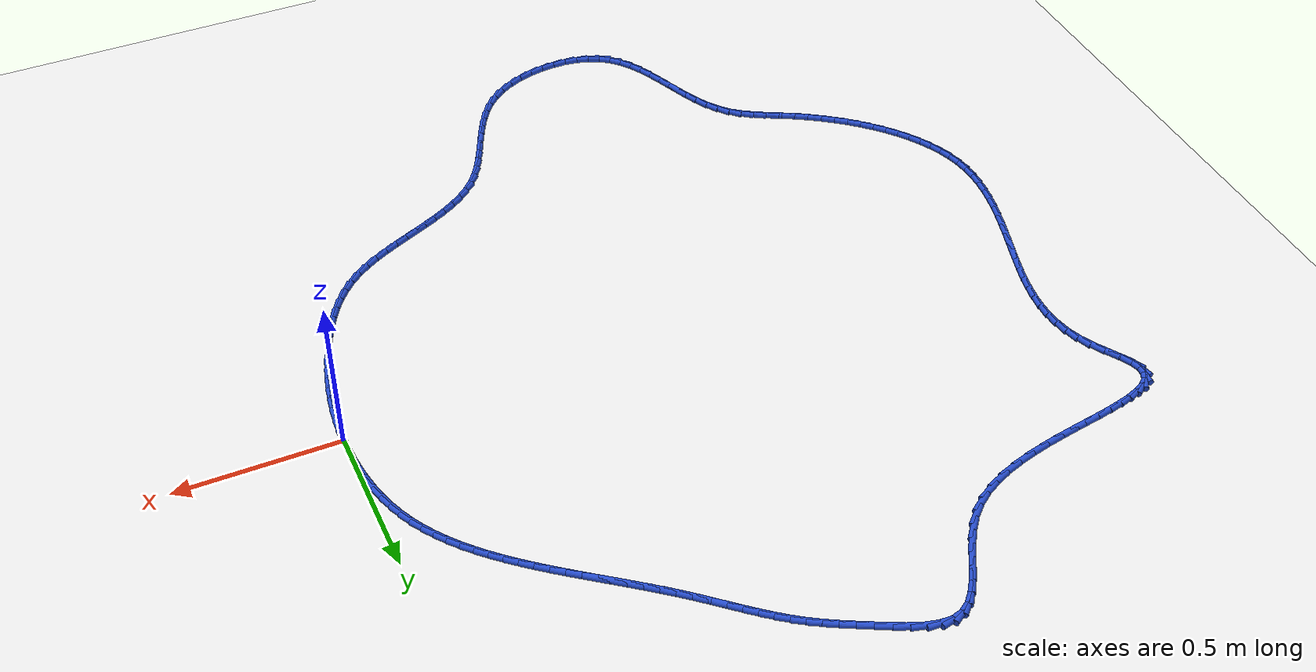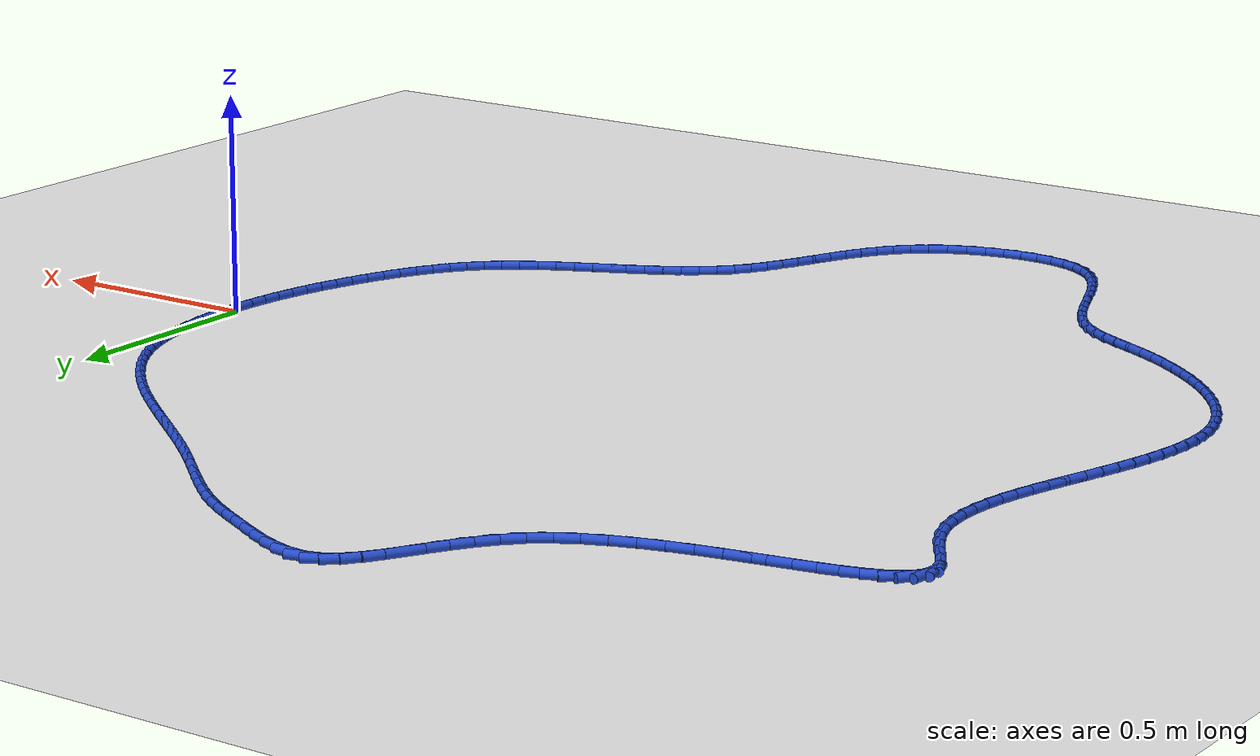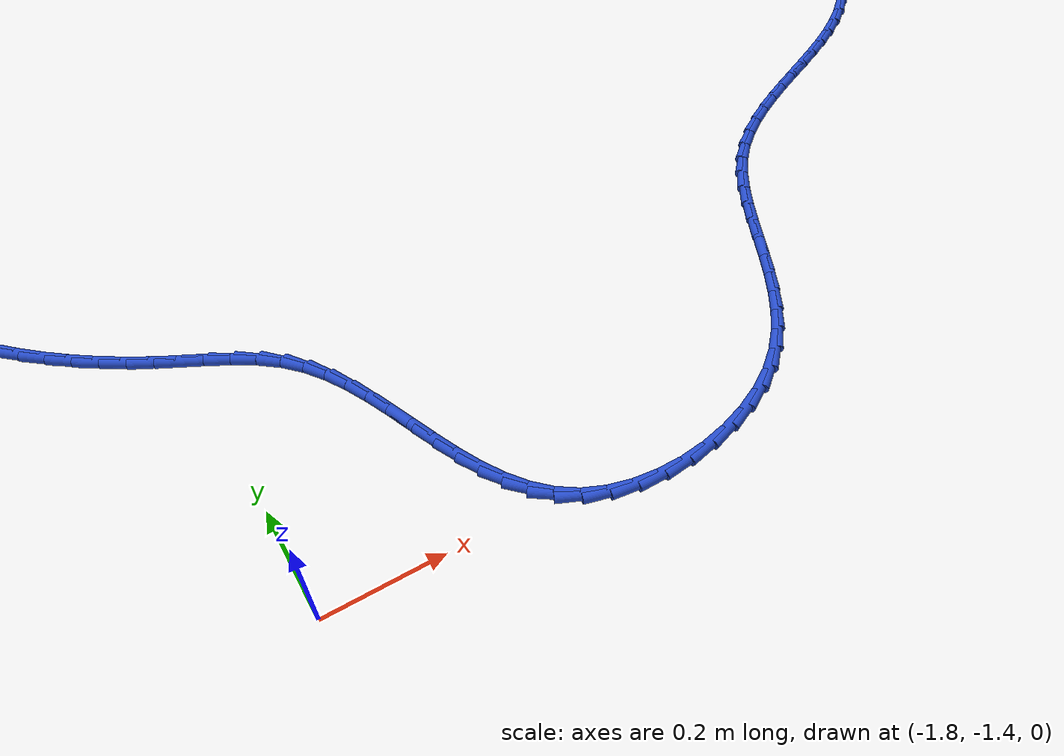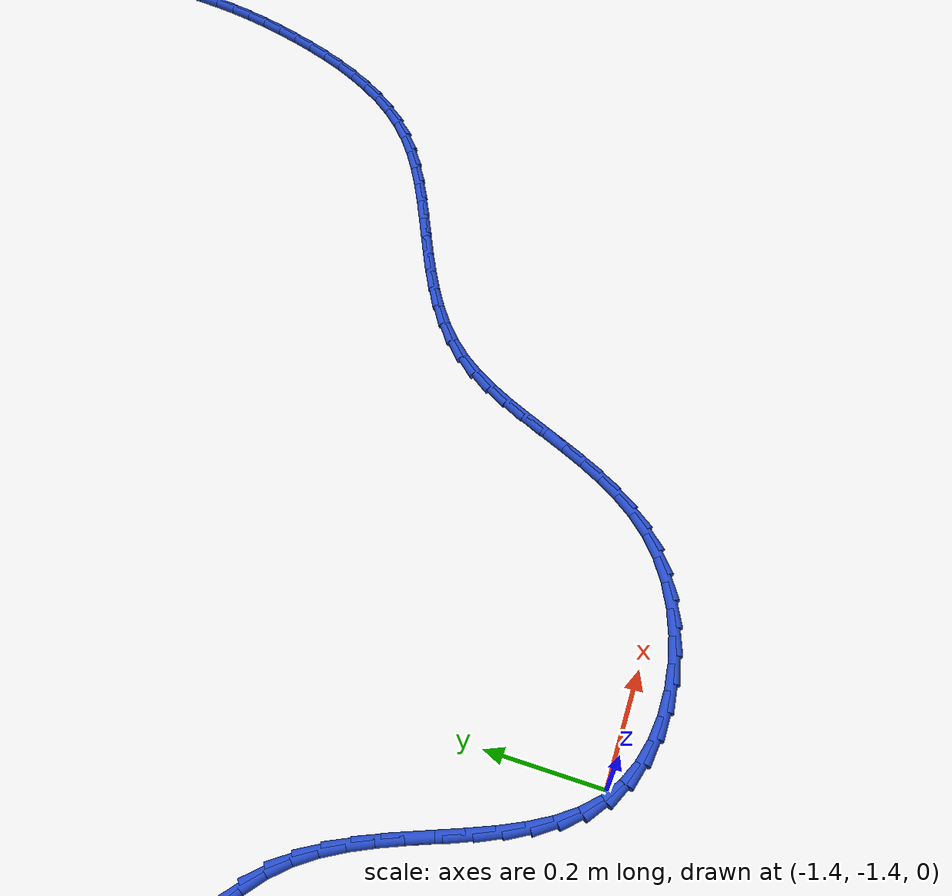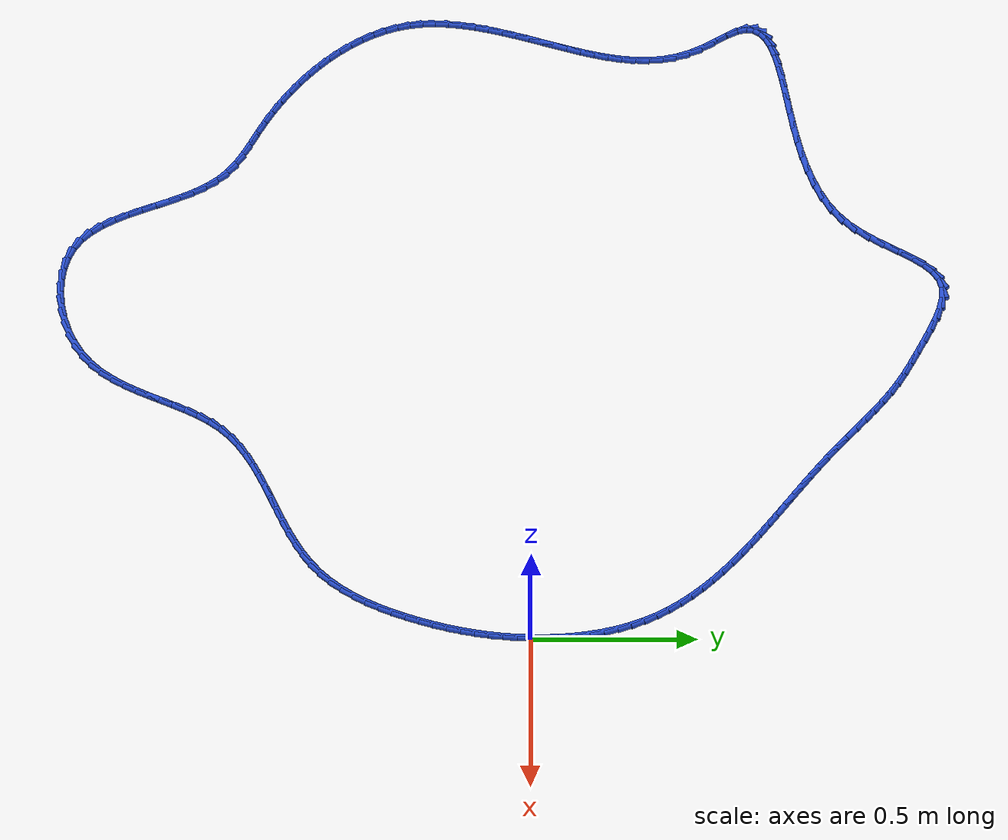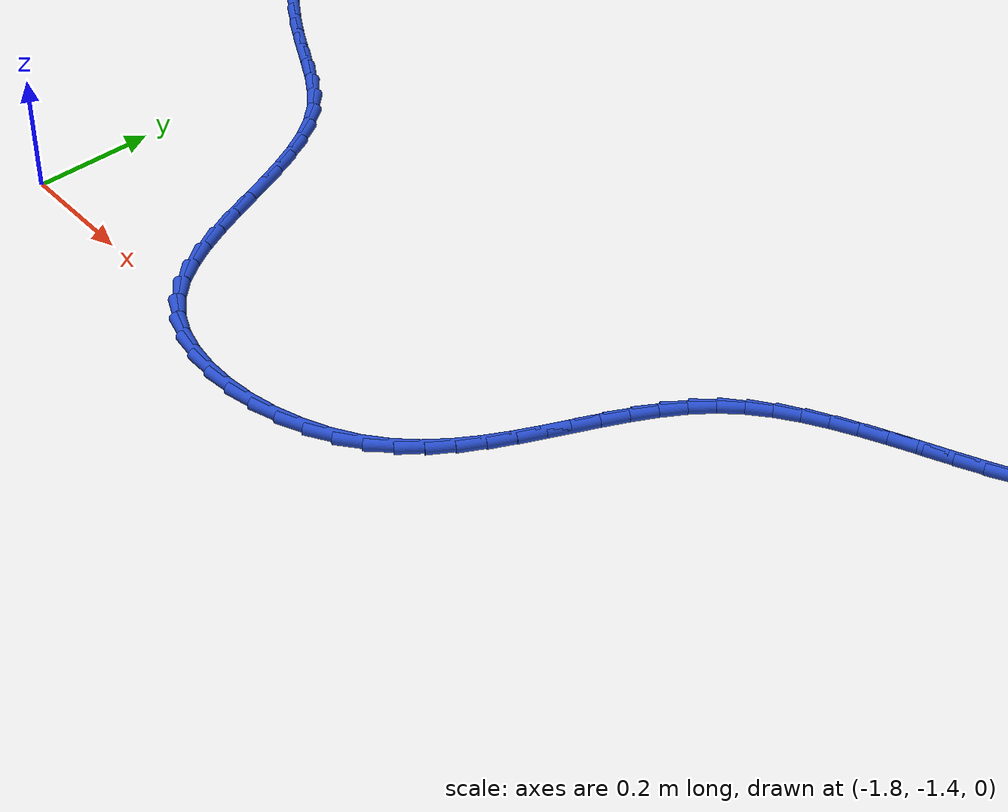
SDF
<sdf version="1.6">
 <world name="default">
  <light name="sun" type="directional">
   <pose>0 0 10 0 -0 0</pose>
   <diffuse>0.8 0.8 0.8 1</diffuse>
   <specular>0.2 0.2 0.2 1</specular>
   <attenuation>
    <range>1000</range>
    <constant>0.9</constant>
    <linear>0.01</linear>
    <quadratic>0.001</quadratic>
   </attenuation>
   <direction>-0.5 0.1 -0.9</direction>
  </light>
  <model name="ground_plane">
   <static>1</static>
   <link name="link">
    <collision name="collision">
     <geometry><plane><normal>0 0 1</normal><size>100 100</size></plane></geometry>
     <surface><friction><ode><mu>100</mu><mu2>50</mu2></ode></friction></surface>
    </collision>
    <visual name="visual">
     <cast_shadows>0</cast_shadows>
     <geometry><plane><normal>0 0 1</normal><size>100 100</size></plane></geometry>
     <material>
      <script><uri>file://media/materials/scripts/gazebo.material</uri><name>Gazebo/WhiteGlow</name></script>
     </material>
    </visual>
   </link>
  </model>
  <gravity>0 0 -9.8</gravity>
  <magnetic_field>6e-06 2.3e-05 -4.2e-05</magnetic_field>
  <atmosphere type="adiabatic"/>
  <physics name="default_physics" default="0" type="ode">
   <max_step_size>0.001</max_step_size>
   <real_time_factor>1</real_time_factor>
   <real_time_update_rate>1000</real_time_update_rate>
  </physics>
  <scene><ambient>0.4 0.4 0.4 1</ambient><background>0.7 0.7 0.7 1</background><shadows>1</shadows></scene>
  <spherical_coordinates>
   <surface_model>EARTH_WGS84</surface_model>
   <latitude_deg>0</latitude_deg>
   <longitude_deg>0</longitude_deg>
   <elevation>0</elevation>
   <heading_deg>0</heading_deg>
  </spherical_coordinates>
  <model name="line">
   <link name="link_0">
    <pose>2.6020852139652106e-18 6.938893903907228e-17 0.01 0 1.57 -1.5685525435773073</pose>
    <collision name="collision">
     <geometry><cylinder><radius>0.01</radius><length>0.08</length></cylinder></geometry>
    </collision>
    <visual name="visual">
     <material>
      <script><name>Gazebo/Blue</name><uri>file://media/materials/scripts/gazebo.material</uri></script>
     </material>
     <geometry><cylinder><radius>0.01</radius><length>0.08</length></cylinder></geometry>
    </visual>
   </link>
   <link name="link_1">
    <pose>-9.700862294422992e-05 0.04323432824750585 0.01 0 1.57 -1.526157090669468</pose>
    <collision name="collision">
     <geometry><cylinder><radius>0.01</radius><length>0.08</length></cylinder></geometry>
    </collision>
    <visual name="visual">
     <material>
      <script><name>Gazebo/Blue</name><uri>file://media/materials/scripts/gazebo.material</uri></script>
     </material>
     <geometry><cylinder><radius>0.01</radius><length>0.08</length></cylinder></geometry>
    </visual>
   </link>
   <link name="link_2">
    <pose>-0.0020345948504014 0.08661094577264346 0.01 0 1.57 -1.481457483727426</pose>
    <collision name="collision">
     <geometry><cylinder><radius>0.01</radius><length>0.08</length></cylinder></geometry>
    </collision>
    <visual name="visual">
     <material>
      <script><name>Gazebo/Blue</name><uri>file://media/materials/scripts/gazebo.material</uri></script>
     </material>
     <geometry><cylinder><radius>0.01</radius><length>0.08</length></cylinder></geometry>
    </visual>
   </link>
   <link name="link_3">
    <pose>-0.005911129818629876 0.12988681452351736 0.01 0 1.57 -1.4339087129957682</pose>
    <collision name="collision">
     <geometry><cylinder><radius>0.01</radius><length>0.08</length></cylinder></geometry>
    </collision>
    <visual name="visual">
     <material>
      <script><name>Gazebo/Blue</name><uri>file://media/materials/scripts/gazebo.material</uri></script>
     </material>
     <geometry><cylinder><radius>0.01</radius><length>0.08</length></cylinder></geometry>
    </visual>
   </link>
   <link name="link_4">
    <pose>-0.011824984663888063 0.17281889644823215 0.01 0 1.57 -1.3829444190439464</pose>
    <collision name="collision">
     <geometry><cylinder><radius>0.01</radius><length>0.08</length></cylinder></geometry>
    </collision>
    <visual name="visual">
     <material>
      <script><name>Gazebo/Blue</name><uri>file://media/materials/scripts/gazebo.material</uri></script>
     </material>
     <geometry><cylinder><radius>0.01</radius><length>0.08</length></cylinder></geometry>
    </visual>
   </link>
   <link name="link_5">
    <pose>-0.01987453052243432 0.21516415349489235 0.01 0 1.57 -1.3279779806215533</pose>
    <collision name="collision">
     <geometry><cylinder><radius>0.01</radius><length>0.08</length></cylinder></geometry>
    </collision>
    <visual name="visual">
     <material>
      <script><name>Gazebo/Blue</name><uri>file://media/materials/scripts/gazebo.material</uri></script>
     </material>
     <geometry><cylinder><radius>0.01</radius><length>0.08</length></cylinder></geometry>
    </visual>
   </link>
   <link name="link_6">
    <pose>-0.030158138530527026 0.25667954761160244 0.01 0 1.57 -1.2684124791670501</pose>
    <collision name="collision">
     <geometry><cylinder><radius>0.01</radius><length>0.08</length></cylinder></geometry>
    </collision>
    <visual name="visual">
     <material>
      <script><name>Gazebo/Blue</name><uri>file://media/materials/scripts/gazebo.material</uri></script>
     </material>
     <geometry><cylinder><radius>0.01</radius><length>0.08</length></cylinder></geometry>
    </visual>
   </link>
   <link name="link_7">
    <pose>-0.04277417982442458 0.29712204074646703 0.01 0 1.57 -1.2036632140516401</pose>
    <collision name="collision">
     <geometry><cylinder><radius>0.01</radius><length>0.08</length></cylinder></geometry>
    </collision>
    <visual name="visual">
     <material>
      <script><name>Gazebo/Blue</name><uri>file://media/materials/scripts/gazebo.material</uri></script>
     </material>
     <geometry><cylinder><radius>0.01</radius><length>0.08</length></cylinder></geometry>
    </visual>
   </link>
   <link name="link_8">
    <pose>-0.05782102554038537 0.3362485948475908 0.01 0 1.57 -1.1341719705778326</pose>
    <collision name="collision">
     <geometry><cylinder><radius>0.01</radius><length>0.08</length></cylinder></geometry>
    </collision>
    <visual name="visual">
     <material>
      <script><name>Gazebo/Blue</name><uri>file://media/materials/scripts/gazebo.material</uri></script>
     </material>
     <geometry><cylinder><radius>0.01</radius><length>0.08</length></cylinder></geometry>
    </visual>
   </link>
   <link name="link_9">
    <pose>-0.07536937202131329 0.373852469561113 0.01 0 1.57 -1.0660788415146025</pose>
    <collision name="collision">
     <geometry><cylinder><radius>0.01</radius><length>0.08</length></cylinder></geometry>
    </collision>
    <visual name="visual">
     <material>
      <script><name>Gazebo/Blue</name><uri>file://media/materials/scripts/gazebo.material</uri></script>
     </material>
     <geometry><cylinder><radius>0.01</radius><length>0.08</length></cylinder></geometry>
    </visual>
   </link>
   <link name="link_10">
    <pose>-0.09531484360284005 0.4099565454294516 0.01 0 1.57 -1.0024793015918327</pose>
    <collision name="collision">
     <geometry><cylinder><radius>0.01</radius><length>0.08</length></cylinder></geometry>
    </collision>
    <visual name="visual">
     <material>
      <script><name>Gazebo/Blue</name><uri>file://media/materials/scripts/gazebo.material</uri></script>
     </material>
     <geometry><cylinder><radius>0.01</radius><length>0.08</length></cylinder></geometry>
    </visual>
   </link>
   <link name="link_11">
    <pose>-0.11748480464907832 0.4446732313901359 0.01 0 1.57 -0.9439532809843925</pose>
    <collision name="collision">
     <geometry><cylinder><radius>0.01</radius><length>0.08</length></cylinder></geometry>
    </collision>
    <visual name="visual">
     <material>
      <script><name>Gazebo/Blue</name><uri>file://media/materials/scripts/gazebo.material</uri></script>
     </material>
     <geometry><cylinder><radius>0.01</radius><length>0.08</length></cylinder></geometry>
    </visual>
   </link>
   <link name="link_12">
    <pose>-0.14170646449625524 0.47811513971212805 0.01 0 1.57 -0.8908490246325244</pose>
    <collision name="collision">
     <geometry><cylinder><radius>0.01</radius><length>0.08</length></cylinder></geometry>
    </collision>
    <visual name="visual">
     <material>
      <script><name>Gazebo/Blue</name><uri>file://media/materials/scripts/gazebo.material</uri></script>
     </material>
     <geometry><cylinder><radius>0.01</radius><length>0.08</length></cylinder></geometry>
    </visual>
   </link>
   <link name="link_13">
    <pose>-0.16780703248059795 0.5103948826643905 0.01 0 1.57 -0.8433225476517466</pose>
    <collision name="collision">
     <geometry><cylinder><radius>0.01</radius><length>0.08</length></cylinder></geometry>
    </collision>
    <visual name="visual">
     <material>
      <script><name>Gazebo/Blue</name><uri>file://media/materials/scripts/gazebo.material</uri></script>
     </material>
     <geometry><cylinder><radius>0.01</radius><length>0.08</length></cylinder></geometry>
    </visual>
   </link>
   <link name="link_14">
    <pose>-0.19561371793833351 0.5416250725158849 0.01 0 1.57 -0.80138178652893</pose>
    <collision name="collision">
     <geometry><cylinder><radius>0.01</radius><length>0.08</length></cylinder></geometry>
    </collision>
    <visual name="visual">
     <material>
      <script><name>Gazebo/Blue</name><uri>file://media/materials/scripts/gazebo.material</uri></script>
     </material>
     <geometry><cylinder><radius>0.01</radius><length>0.08</length></cylinder></geometry>
    </visual>
   </link>
   <link name="link_15">
    <pose>-0.2249537302056891 0.5719183215355734 0.01 0 1.57 -0.7649317041077852</pose>
    <collision name="collision">
     <geometry><cylinder><radius>0.01</radius><length>0.08</length></cylinder></geometry>
    </collision>
    <visual name="visual">
     <material>
      <script><name>Gazebo/Blue</name><uri>file://media/materials/scripts/gazebo.material</uri></script>
     </material>
     <geometry><cylinder><radius>0.01</radius><length>0.08</length></cylinder></geometry>
    </visual>
   </link>
   <link name="link_16">
    <pose>-0.2556542786188917 0.6013872419924183 0.01 0 1.57 -0.7338145800664079</pose>
    <collision name="collision">
     <geometry><cylinder><radius>0.01</radius><length>0.08</length></cylinder></geometry>
    </collision>
    <visual name="visual">
     <material>
      <script><name>Gazebo/Blue</name><uri>file://media/materials/scripts/gazebo.material</uri></script>
     </material>
     <geometry><cylinder><radius>0.01</radius><length>0.08</length></cylinder></geometry>
    </visual>
   </link>
   <link name="link_17">
    <pose>-0.2875425725141685 0.6301444461553818 0.01 0 1.57 -0.7078428669132037</pose>
    <collision name="collision">
     <geometry><cylinder><radius>0.01</radius><length>0.08</length></cylinder></geometry>
    </collision>
    <visual name="visual">
     <material>
      <script><name>Gazebo/Blue</name><uri>file://media/materials/scripts/gazebo.material</uri></script>
     </material>
     <geometry><cylinder><radius>0.01</radius><length>0.08</length></cylinder></geometry>
    </visual>
   </link>
   <link name="link_18">
    <pose>-0.32044582122774656 0.6583025462934258 0.01 0 1.57 -0.6868242028342659</pose>
    <collision name="collision">
     <geometry><cylinder><radius>0.01</radius><length>0.08</length></cylinder></geometry>
    </collision>
    <visual name="visual">
     <material>
      <script><name>Gazebo/Blue</name><uri>file://media/materials/scripts/gazebo.material</uri></script>
     </material>
     <geometry><cylinder><radius>0.01</radius><length>0.08</length></cylinder></geometry>
    </visual>
   </link>
   <link name="link_19">
    <pose>-0.35419123409585307 0.6859741546755121 0.01 0 1.57 -0.6705794047479512</pose>
    <collision name="collision">
     <geometry><cylinder><radius>0.01</radius><length>0.08</length></cylinder></geometry>
    </collision>
    <visual name="visual">
     <material>
      <script><name>Gazebo/Blue</name><uri>file://media/materials/scripts/gazebo.material</uri></script>
     </material>
     <geometry><cylinder><radius>0.01</radius><length>0.08</length></cylinder></geometry>
    </visual>
   </link>
   <link name="link_20">
    <pose>-0.38860602045471504 0.7132718835706032 0.01 0 1.57 -0.6589547551014436</pose>
    <collision name="collision">
     <geometry><cylinder><radius>0.01</radius><length>0.08</length></cylinder></geometry>
    </collision>
    <visual name="visual">
     <material>
      <script><name>Gazebo/Blue</name><uri>file://media/materials/scripts/gazebo.material</uri></script>
     </material>
     <geometry><cylinder><radius>0.01</radius><length>0.08</length></cylinder></geometry>
    </visual>
   </link>
   <link name="link_21">
    <pose>-0.42351738964055985 0.7403083452476616 0.01 0 1.57 -0.6518299279442448</pose>
    <collision name="collision">
     <geometry><cylinder><radius>0.01</radius><length>0.08</length></cylinder></geometry>
    </collision>
    <visual name="visual">
     <material>
      <script><name>Gazebo/Blue</name><uri>file://media/materials/scripts/gazebo.material</uri></script>
     </material>
     <geometry><cylinder><radius>0.01</radius><length>0.08</length></cylinder></geometry>
    </visual>
   </link>
   <link name="link_22">
    <pose>-0.45875255098961426 0.7671961519756487 0.01 0 1.57 -0.6491226973160237</pose>
    <collision name="collision">
     <geometry><cylinder><radius>0.01</radius><length>0.08</length></cylinder></geometry>
    </collision>
    <visual name="visual">
     <material>
      <script><name>Gazebo/Blue</name><uri>file://media/materials/scripts/gazebo.material</uri></script>
     </material>
     <geometry><cylinder><radius>0.01</radius><length>0.08</length></cylinder></geometry>
    </visual>
   </link>
   <link name="link_23">
    <pose>-0.4941387138381055 0.7940479160235268 0.01 0 1.57 -0.6507912752699311</pose>
    <collision name="collision">
     <geometry><cylinder><radius>0.01</radius><length>0.08</length></cylinder></geometry>
    </collision>
    <visual name="visual">
     <material>
      <script><name>Gazebo/Blue</name><uri>file://media/materials/scripts/gazebo.material</uri></script>
     </material>
     <geometry><cylinder><radius>0.01</radius><length>0.08</length></cylinder></geometry>
    </visual>
   </link>
   <link name="link_24">
    <pose>-0.5295030875222605 0.8209762496602578 0.01 0 1.57 -0.656834811406058</pose>
    <collision name="collision">
     <geometry><cylinder><radius>0.01</radius><length>0.08</length></cylinder></geometry>
    </collision>
    <visual name="visual">
     <material>
      <script><name>Gazebo/Blue</name><uri>file://media/materials/scripts/gazebo.material</uri></script>
     </material>
     <geometry><cylinder><radius>0.01</radius><length>0.08</length></cylinder></geometry>
    </visual>
   </link>
   <link name="link_25">
    <pose>-0.5646728813783068 0.8480937651548044 0.01 0 1.57 -0.6672922797007735</pose>
    <collision name="collision">
     <geometry><cylinder><radius>0.01</radius><length>0.08</length></cylinder></geometry>
    </collision>
    <visual name="visual">
     <material>
      <script><name>Gazebo/Blue</name><uri>file://media/materials/scripts/gazebo.material</uri></script>
     </material>
     <geometry><cylinder><radius>0.01</radius><length>0.08</length></cylinder></geometry>
    </visual>
   </link>
   <link name="link_26">
    <pose>-0.5994753047424713 0.8755130747761283 0.01 0 1.57 -0.6822396869788577</pose>
    <collision name="collision">
     <geometry><cylinder><radius>0.01</radius><length>0.08</length></cylinder></geometry>
    </collision>
    <visual name="visual">
     <material>
      <script><name>Gazebo/Blue</name><uri>file://media/materials/scripts/gazebo.material</uri></script>
     </material>
     <geometry><cylinder><radius>0.01</radius><length>0.08</length></cylinder></geometry>
    </visual>
   </link>
   <link name="link_27">
    <pose>-0.6337375669509808 0.9033467907931914 0.01 0 1.57 -0.7015863751057289</pose>
    <collision name="collision">
     <geometry><cylinder><radius>0.01</radius><length>0.08</length></cylinder></geometry>
    </collision>
    <visual name="visual">
     <material>
      <script><name>Gazebo/Blue</name><uri>file://media/materials/scripts/gazebo.material</uri></script>
     </material>
     <geometry><cylinder><radius>0.01</radius><length>0.08</length></cylinder></geometry>
    </visual>
   </link>
   <link name="link_28">
    <pose>-0.667292698881509 0.9317010061118095 0.01 0 1.57 -0.7191388566225841</pose>
    <collision name="collision">
     <geometry><cylinder><radius>0.01</radius><length>0.08</length></cylinder></geometry>
    </collision>
    <visual name="visual">
     <material>
      <script><name>Gazebo/Blue</name><uri>file://media/materials/scripts/gazebo.material</uri></script>
     </material>
     <geometry><cylinder><radius>0.01</radius><length>0.08</length></cylinder></geometry>
    </visual>
   </link>
   <link name="link_29">
    <pose>-0.7001576919193321 0.960475801988674 0.01 0 1.57 -0.7274101344294757</pose>
    <collision name="collision">
     <geometry><cylinder><radius>0.01</radius><length>0.08</length></cylinder></geometry>
    </collision>
    <visual name="visual">
     <material>
      <script><name>Gazebo/Blue</name><uri>file://media/materials/scripts/gazebo.material</uri></script>
     </material>
     <geometry><cylinder><radius>0.01</radius><length>0.08</length></cylinder></geometry>
    </visual>
   </link>
   <link name="link_30">
    <pose>-0.7325665418395403 0.9893282432157199 0.01 0 1.57 -0.7258031718105259</pose>
    <collision name="collision">
     <geometry><cylinder><radius>0.01</radius><length>0.08</length></cylinder></geometry>
    </collision>
    <visual name="visual">
     <material>
      <script><name>Gazebo/Blue</name><uri>file://media/materials/scripts/gazebo.material</uri></script>
     </material>
     <geometry><cylinder><radius>0.01</radius><length>0.08</length></cylinder></geometry>
    </visual>
   </link>
   <link name="link_31">
    <pose>-0.7647657313230898 1.017901410887493 0.01 0 1.57 -0.7140747260560818</pose>
    <collision name="collision">
     <geometry><cylinder><radius>0.01</radius><length>0.08</length></cylinder></geometry>
    </collision>
    <visual name="visual">
     <material>
      <script><name>Gazebo/Blue</name><uri>file://media/materials/scripts/gazebo.material</uri></script>
     </material>
     <geometry><cylinder><radius>0.01</radius><length>0.08</length></cylinder></geometry>
    </visual>
   </link>
   <link name="link_32">
    <pose>-0.7970017430509369 1.0458383860985394 0.01 0 1.57 -0.6919083852375368</pose>
    <collision name="collision">
     <geometry><cylinder><radius>0.01</radius><length>0.08</length></cylinder></geometry>
    </collision>
    <visual name="visual">
     <material>
      <script><name>Gazebo/Blue</name><uri>file://media/materials/scripts/gazebo.material</uri></script>
     </material>
     <geometry><cylinder><radius>0.01</radius><length>0.08</length></cylinder></geometry>
    </visual>
   </link>
   <link name="link_33">
    <pose>-0.8295210597040381 1.072782249943405 0.01 0 1.57 -0.6589465915032207</pose>
    <collision name="collision">
     <geometry><cylinder><radius>0.01</radius><length>0.08</length></cylinder></geometry>
    </collision>
    <visual name="visual">
     <material>
      <script><name>Gazebo/Blue</name><uri>file://media/materials/scripts/gazebo.material</uri></script>
     </material>
     <geometry><cylinder><radius>0.01</radius><length>0.08</length></cylinder></geometry>
    </visual>
   </link>
   <link name="link_34">
    <pose>-0.8625701639633494 1.098376083516635 0.01 0 1.57 -0.6148631902702463</pose>
    <collision name="collision">
     <geometry><cylinder><radius>0.01</radius><length>0.08</length></cylinder></geometry>
    </collision>
    <visual name="visual">
     <material>
      <script><name>Gazebo/Blue</name><uri>file://media/materials/scripts/gazebo.material</uri></script>
     </material>
     <geometry><cylinder><radius>0.01</radius><length>0.08</length></cylinder></geometry>
    </visual>
   </link>
   <link name="link_35">
    <pose>-0.8963955385098271 1.1222629679127754 0.01 0 1.57 -0.5618458516017223</pose>
    <collision name="collision">
     <geometry><cylinder><radius>0.01</radius><length>0.08</length></cylinder></geometry>
    </collision>
    <visual name="visual">
     <material>
      <script><name>Gazebo/Blue</name><uri>file://media/materials/scripts/gazebo.material</uri></script>
     </material>
     <geometry><cylinder><radius>0.01</radius><length>0.08</length></cylinder></geometry>
    </visual>
   </link>
   <link name="link_36">
    <pose>-0.9312535462861457 1.144206917255133 0.01 0 1.57 -0.51687509385871</pose>
    <collision name="collision">
     <geometry><cylinder><radius>0.01</radius><length>0.08</length></cylinder></geometry>
    </collision>
    <visual name="visual">
     <material>
      <script><name>Gazebo/Blue</name><uri>file://media/materials/scripts/gazebo.material</uri></script>
     </material>
     <geometry><cylinder><radius>0.01</radius><length>0.08</length></cylinder></geometry>
    </visual>
   </link>
   <link name="link_37">
    <pose>-0.9674675212022595 1.164791660988698 0.01 0 1.57 -0.4884160553401611</pose>
    <collision name="collision">
     <geometry><cylinder><radius>0.01</radius><length>0.08</length></cylinder></geometry>
    </collision>
    <visual name="visual">
     <material>
      <script><name>Gazebo/Blue</name><uri>file://media/materials/scripts/gazebo.material</uri></script>
     </material>
     <geometry><cylinder><radius>0.01</radius><length>0.08</length></cylinder></geometry>
    </visual>
   </link>
   <link name="link_38">
    <pose>-1.005388599582561 1.184941226242959 0.01 0 1.57 -0.47653960126167877</pose>
    <collision name="collision">
     <geometry><cylinder><radius>0.01</radius><length>0.08</length></cylinder></geometry>
    </collision>
    <visual name="visual">
     <material>
      <script><name>Gazebo/Blue</name><uri>file://media/materials/scripts/gazebo.material</uri></script>
     </material>
     <geometry><cylinder><radius>0.01</radius><length>0.08</length></cylinder></geometry>
    </visual>
   </link>
   <link name="link_39">
    <pose>-1.04536704280676 1.2055789160305022 0.01 0 1.57 -0.46850079729720323</pose>
    <collision name="collision">
     <geometry><cylinder><radius>0.01</radius><length>0.08</length></cylinder></geometry>
    </collision>
    <visual name="visual">
     <material>
      <script><name>Gazebo/Blue</name><uri>file://media/materials/scripts/gazebo.material</uri></script>
     </material>
     <geometry><cylinder><radius>0.01</radius><length>0.08</length></cylinder></geometry>
    </visual>
   </link>
   <link name="link_40">
    <pose>-1.0873217931283763 1.2268114301923025 0.01 0 1.57 -0.4344861967894188</pose>
    <collision name="collision">
     <geometry><cylinder><radius>0.01</radius><length>0.08</length></cylinder></geometry>
    </collision>
    <visual name="visual">
     <material>
      <script><name>Gazebo/Blue</name><uri>file://media/materials/scripts/gazebo.material</uri></script>
     </material>
     <geometry><cylinder><radius>0.01</radius><length>0.08</length></cylinder></geometry>
    </visual>
   </link>
   <link name="link_41">
    <pose>-1.1300628437960494 1.2466459296906856 0.01 0 1.57 -0.3650000847591498</pose>
    <collision name="collision">
     <geometry><cylinder><radius>0.01</radius><length>0.08</length></cylinder></geometry>
    </collision>
    <visual name="visual">
     <material>
      <script><name>Gazebo/Blue</name><uri>file://media/materials/scripts/gazebo.material</uri></script>
     </material>
     <geometry><cylinder><radius>0.01</radius><length>0.08</length></cylinder></geometry>
    </visual>
   </link>
   <link name="link_42">
    <pose>-1.1722244218648865 1.2627568027858482 0.01 0 1.57 -0.24515538938612375</pose>
    <collision name="collision">
     <geometry><cylinder><radius>0.01</radius><length>0.08</length></cylinder></geometry>
    </collision>
    <visual name="visual">
     <material>
      <script><name>Gazebo/Blue</name><uri>file://media/materials/scripts/gazebo.material</uri></script>
     </material>
     <geometry><cylinder><radius>0.01</radius><length>0.08</length></cylinder></geometry>
    </visual>
   </link>
   <link name="link_43">
    <pose>-1.2124407543899938 1.2728184377379888 0.01 0 1.57 -0.045673963490169944</pose>
    <collision name="collision">
     <geometry><cylinder><radius>0.01</radius><length>0.08</length></cylinder></geometry>
    </collision>
    <visual name="visual">
     <material>
      <script><name>Gazebo/Blue</name><uri>file://media/materials/scripts/gazebo.material</uri></script>
     </material>
     <geometry><cylinder><radius>0.01</radius><length>0.08</length></cylinder></geometry>
    </visual>
   </link>
   <link name="link_44">
    <pose>-1.2493460684264779 1.274505222807305 0.01 0 1.57 0.2624191395198274</pose>
    <collision name="collision">
     <geometry><cylinder><radius>0.01</radius><length>0.08</length></cylinder></geometry>
    </collision>
    <visual name="visual">
     <material>
      <script><name>Gazebo/Blue</name><uri>file://media/materials/scripts/gazebo.material</uri></script>
     </material>
     <geometry><cylinder><radius>0.01</radius><length>0.08</length></cylinder></geometry>
    </visual>
   </link>
   <link name="link_45">
    <pose>-1.2817631740574642 1.2657975489592763 0.01 0 1.57 0.5812949593078</pose>
    <collision name="collision">
     <geometry><cylinder><radius>0.01</radius><length>0.08</length></cylinder></geometry>
    </collision>
    <visual name="visual">
     <material>
      <script><name>Gazebo/Blue</name><uri>file://media/materials/scripts/gazebo.material</uri></script>
     </material>
     <geometry><cylinder><radius>0.01</radius><length>0.08</length></cylinder></geometry>
    </visual>
   </link>
   <link name="link_46">
    <pose>-1.3100700731833486 1.247199326419396 0.01 0 1.57 0.8123134432065343</pose>
    <collision name="collision">
     <geometry><cylinder><radius>0.01</radius><length>0.08</length></cylinder></geometry>
    </collision>
    <visual name="visual">
     <material>
      <script><name>Gazebo/Blue</name><uri>file://media/materials/scripts/gazebo.material</uri></script>
     </material>
     <geometry><cylinder><radius>0.01</radius><length>0.08</length></cylinder></geometry>
    </visual>
   </link>
   <link name="link_47">
    <pose>-1.3354104093544796 1.2204568275632617 0.01 0 1.57 0.9534069685751563</pose>
    <collision name="collision">
     <geometry><cylinder><radius>0.01</radius><length>0.08</length></cylinder></geometry>
    </collision>
    <visual name="visual">
     <material>
      <script><name>Gazebo/Blue</name><uri>file://media/materials/scripts/gazebo.material</uri></script>
     </material>
     <geometry><cylinder><radius>0.01</radius><length>0.08</length></cylinder></geometry>
    </visual>
   </link>
   <link name="link_48">
    <pose>-1.3589331773752757 1.1873250079350381 0.01 0 1.57 1.0265988983784917</pose>
    <collision name="collision">
     <geometry><cylinder><radius>0.01</radius><length>0.08</length></cylinder></geometry>
    </collision>
    <visual name="visual">
     <material>
      <script><name>Gazebo/Blue</name><uri>file://media/materials/scripts/gazebo.material</uri></script>
     </material>
     <geometry><cylinder><radius>0.01</radius><length>0.08</length></cylinder></geometry>
    </visual>
   </link>
   <link name="link_49">
    <pose>-1.3817873720501535 1.1495588230788898 0.01 0 1.57 1.049639048298989</pose>
    <collision name="collision">
     <geometry><cylinder><radius>0.01</radius><length>0.08</length></cylinder></geometry>
    </collision>
    <visual name="visual">
     <material>
      <script><name>Gazebo/Blue</name><uri>file://media/materials/scripts/gazebo.material</uri></script>
     </material>
     <geometry><cylinder><radius>0.01</radius><length>0.08</length></cylinder></geometry>
    </visual>
   </link>
   <link name="link_50">
    <pose>-1.4051219881835284 1.1089132285389807 0.01 0 1.57 1.032103687482029</pose>
    <collision name="collision">
     <geometry><cylinder><radius>0.01</radius><length>0.08</length></cylinder></geometry>
    </collision>
    <visual name="visual">
     <material>
      <script><name>Gazebo/Blue</name><uri>file://media/materials/scripts/gazebo.material</uri></script>
     </material>
     <geometry><cylinder><radius>0.01</radius><length>0.08</length></cylinder></geometry>
    </visual>
   </link>
   <link name="link_51">
    <pose>-1.4300860205798187 1.0671431798594762 0.01 0 1.57 0.9774935093933754</pose>
    <collision name="collision">
     <geometry><cylinder><radius>0.01</radius><length>0.08</length></cylinder></geometry>
    </collision>
    <visual name="visual">
     <material>
      <script><name>Gazebo/Blue</name><uri>file://media/materials/scripts/gazebo.material</uri></script>
     </material>
     <geometry><cylinder><radius>0.01</radius><length>0.08</length></cylinder></geometry>
    </visual>
   </link>
   <link name="link_52">
    <pose>-1.4578284640434411 1.0260036325845396 0.01 0 1.57 0.8856551137833352</pose>
    <collision name="collision">
     <geometry><cylinder><radius>0.01</radius><length>0.08</length></cylinder></geometry>
    </collision>
    <visual name="visual">
     <material>
      <script><name>Gazebo/Blue</name><uri>file://media/materials/scripts/gazebo.material</uri></script>
     </material>
     <geometry><cylinder><radius>0.01</radius><length>0.08</length></cylinder></geometry>
    </visual>
   </link>
   <link name="link_53">
    <pose>-1.489498313378812 0.9872495422583365 0.01 0 1.57 0.7559021925840036</pose>
    <collision name="collision">
     <geometry><cylinder><radius>0.01</radius><length>0.08</length></cylinder></geometry>
    </collision>
    <visual name="visual">
     <material>
      <script><name>Gazebo/Blue</name><uri>file://media/materials/scripts/gazebo.material</uri></script>
     </material>
     <geometry><cylinder><radius>0.01</radius><length>0.08</length></cylinder></geometry>
    </visual>
   </link>
   <link name="link_54">
    <pose>-1.5262317374903656 0.9526216015159461 0.01 0 1.57 0.612435036888896</pose>
    <collision name="collision">
     <geometry><cylinder><radius>0.01</radius><length>0.08</length></cylinder></geometry>
    </collision>
    <visual name="visual">
     <material>
      <script><name>Gazebo/Blue</name><uri>file://media/materials/scripts/gazebo.material</uri></script>
     </material>
     <geometry><cylinder><radius>0.01</radius><length>0.08</length></cylinder></geometry>
    </visual>
   </link>
   <link name="link_55">
    <pose>-1.5683925100341916 0.923001568865419 0.01 0 1.57 0.49209597525756704</pose>
    <collision name="collision">
     <geometry><cylinder><radius>0.01</radius><length>0.08</length></cylinder></geometry>
    </collision>
    <visual name="visual">
     <material>
      <script><name>Gazebo/Blue</name><uri>file://media/materials/scripts/gazebo.material</uri></script>
     </material>
     <geometry><cylinder><radius>0.01</radius><length>0.08</length></cylinder></geometry>
    </visual>
   </link>
   <link name="link_56">
    <pose>-1.6151455554488932 0.8979380349732585 0.01 0 1.57 0.39598146174606086</pose>
    <collision name="collision">
     <geometry><cylinder><radius>0.01</radius><length>0.08</length></cylinder></geometry>
    </collision>
    <visual name="visual">
     <material>
      <script><name>Gazebo/Blue</name><uri>file://media/materials/scripts/gazebo.material</uri></script>
     </material>
     <geometry><cylinder><radius>0.01</radius><length>0.08</length></cylinder></geometry>
    </visual>
   </link>
   <link name="link_57">
    <pose>-1.6655524798422692 0.8768646964274934 0.01 0 1.57 0.3207672030277832</pose>
    <collision name="collision">
     <geometry><cylinder><radius>0.01</radius><length>0.08</length></cylinder></geometry>
    </collision>
    <visual name="visual">
     <material>
      <script><name>Gazebo/Blue</name><uri>file://media/materials/scripts/gazebo.material</uri></script>
     </material>
     <geometry><cylinder><radius>0.01</radius><length>0.08</length></cylinder></geometry>
    </visual>
   </link>
   <link name="link_58">
    <pose>-1.7186748893221198 0.859215249816153 0.01 0 1.57 0.263185338425875</pose>
    <collision name="collision">
     <geometry><cylinder><radius>0.01</radius><length>0.08</length></cylinder></geometry>
    </collision>
    <visual name="visual">
     <material>
      <script><name>Gazebo/Blue</name><uri>file://media/materials/scripts/gazebo.material</uri></script>
     </material>
     <geometry><cylinder><radius>0.01</radius><length>0.08</length></cylinder></geometry>
    </visual>
   </link>
   <link name="link_59">
    <pose>-1.773574389996243 0.8444233917272663 0.01 0 1.57 0.2206223674119004</pose>
    <collision name="collision">
     <geometry><cylinder><radius>0.01</radius><length>0.08</length></cylinder></geometry>
    </collision>
    <visual name="visual">
     <material>
      <script><name>Gazebo/Blue</name><uri>file://media/materials/scripts/gazebo.material</uri></script>
     </material>
     <geometry><cylinder><radius>0.01</radius><length>0.08</length></cylinder></geometry>
    </visual>
   </link>
   <link name="link_60">
    <pose>-1.8293125879724383 0.8319228187488625 0.01 0 1.57 0.191303111531658</pose>
    <collision name="collision">
     <geometry><cylinder><radius>0.01</radius><length>0.08</length></cylinder></geometry>
    </collision>
    <visual name="visual">
     <material>
      <script><name>Gazebo/Blue</name><uri>file://media/materials/scripts/gazebo.material</uri></script>
     </material>
     <geometry><cylinder><radius>0.01</radius><length>0.08</length></cylinder></geometry>
    </visual>
   </link>
   <link name="link_61">
    <pose>-1.8849510893585042 0.821147227468971 0.01 0 1.57 0.17434441124264227</pose>
    <collision name="collision">
     <geometry><cylinder><radius>0.01</radius><length>0.08</length></cylinder></geometry>
    </collision>
    <visual name="visual">
     <material>
      <script><name>Gazebo/Blue</name><uri>file://media/materials/scripts/gazebo.material</uri></script>
     </material>
     <geometry><cylinder><radius>0.01</radius><length>0.08</length></cylinder></geometry>
    </visual>
   </link>
   <link name="link_62">
    <pose>-1.9395515002622399 0.8115303144756203 0.01 0 1.57 0.1698390735014459</pose>
    <collision name="collision">
     <geometry><cylinder><radius>0.01</radius><length>0.08</length></cylinder></geometry>
    </collision>
    <visual name="visual">
     <material>
      <script><name>Gazebo/Blue</name><uri>file://media/materials/scripts/gazebo.material</uri></script>
     </material>
     <geometry><cylinder><radius>0.01</radius><length>0.08</length></cylinder></geometry>
    </visual>
   </link>
   <link name="link_63">
    <pose>-1.992175426791445 0.80250577635684 0.01 0 1.57 0.17908337595400312</pose>
    <collision name="collision">
     <geometry><cylinder><radius>0.01</radius><length>0.08</length></cylinder></geometry>
    </collision>
    <visual name="visual">
     <material>
      <script><name>Gazebo/Blue</name><uri>file://media/materials/scripts/gazebo.material</uri></script>
     </material>
     <geometry><cylinder><radius>0.01</radius><length>0.08</length></cylinder></geometry>
    </visual>
   </link>
   <link name="link_64">
    <pose>-2.041884475053918 0.7935073097006592 0.01 0 1.57 0.20509047351317902</pose>
    <collision name="collision">
     <geometry><cylinder><radius>0.01</radius><length>0.08</length></cylinder></geometry>
    </collision>
    <visual name="visual">
     <material>
      <script><name>Gazebo/Blue</name><uri>file://media/materials/scripts/gazebo.material</uri></script>
     </material>
     <geometry><cylinder><radius>0.01</radius><length>0.08</length></cylinder></geometry>
    </visual>
   </link>
   <link name="link_65">
    <pose>-2.087740251157458 0.7839686110951072 0.01 0 1.57 0.2536508945192459</pose>
    <collision name="collision">
     <geometry><cylinder><radius>0.01</radius><length>0.08</length></cylinder></geometry>
    </collision>
    <visual name="visual">
     <material>
      <script><name>Gazebo/Blue</name><uri>file://media/materials/scripts/gazebo.material</uri></script>
     </material>
     <geometry><cylinder><radius>0.01</radius><length>0.08</length></cylinder></geometry>
    </visual>
   </link>
   <link name="link_66">
    <pose>-2.1288043612098644 0.7733233771282124 0.01 0 1.57 0.33544277724932886</pose>
    <collision name="collision">
     <geometry><cylinder><radius>0.01</radius><length>0.08</length></cylinder></geometry>
    </collision>
    <visual name="visual">
     <material>
      <script><name>Gazebo/Blue</name><uri>file://media/materials/scripts/gazebo.material</uri></script>
     </material>
     <geometry><cylinder><radius>0.01</radius><length>0.08</length></cylinder></geometry>
    </visual>
   </link>
   <link name="link_67">
    <pose>-2.1641384113189353 0.7610053043880048 0.01 0 1.57 0.46989100430429126</pose>
    <collision name="collision">
     <geometry><cylinder><radius>0.01</radius><length>0.08</length></cylinder></geometry>
    </collision>
    <visual name="visual">
     <material>
      <script><name>Gazebo/Blue</name><uri>file://media/materials/scripts/gazebo.material</uri></script>
     </material>
     <geometry><cylinder><radius>0.01</radius><length>0.08</length></cylinder></geometry>
    </visual>
   </link>
   <link name="link_68">
    <pose>-2.1928040075924713 0.7464480894625136 0.01 0 1.57 0.6894946143160586</pose>
    <collision name="collision">
     <geometry><cylinder><radius>0.01</radius><length>0.08</length></cylinder></geometry>
    </collision>
    <visual name="visual">
     <material>
      <script><name>Gazebo/Blue</name><uri>file://media/materials/scripts/gazebo.material</uri></script>
     </material>
     <geometry><cylinder><radius>0.01</radius><length>0.08</length></cylinder></geometry>
    </visual>
   </link>
   <link name="link_69">
    <pose>-2.213862756138269 0.7290854289397668 0.01 0 1.57 1.0277969908255424</pose>
    <collision name="collision">
     <geometry><cylinder><radius>0.01</radius><length>0.08</length></cylinder></geometry>
    </collision>
    <visual name="visual">
     <material>
      <script><name>Gazebo/Blue</name><uri>file://media/materials/scripts/gazebo.material</uri></script>
     </material>
     <geometry><cylinder><radius>0.01</radius><length>0.08</length></cylinder></geometry>
    </visual>
   </link>
   <link name="link_70">
    <pose>-2.22637626306413 0.7083510194077949 0.01 0 1.57 1.4486043525756949</pose>
    <collision name="collision">
     <geometry><cylinder><radius>0.01</radius><length>0.08</length></cylinder></geometry>
    </collision>
    <visual name="visual">
     <material>
      <script><name>Gazebo/Blue</name><uri>file://media/materials/scripts/gazebo.material</uri></script>
     </material>
     <geometry><cylinder><radius>0.01</radius><length>0.08</length></cylinder></geometry>
    </visual>
   </link>
   <link name="link_71">
    <pose>-2.229406134477852 0.683678557454626 0.01 0 1.57 -1.3228648958778562</pose>
    <collision name="collision">
     <geometry><cylinder><radius>0.01</radius><length>0.08</length></cylinder></geometry>
    </collision>
    <visual name="visual">
     <material>
      <script><name>Gazebo/Blue</name><uri>file://media/materials/scripts/gazebo.material</uri></script>
     </material>
     <geometry><cylinder><radius>0.01</radius><length>0.08</length></cylinder></geometry>
    </visual>
   </link>
   <link name="link_72">
    <pose>-2.222020875485342 0.6545039133024687 0.01 0 1.57 -1.1000312867171587</pose>
    <collision name="collision">
     <geometry><cylinder><radius>0.01</radius><length>0.08</length></cylinder></geometry>
    </collision>
    <visual name="visual">
     <material>
      <script><name>Gazebo/Blue</name><uri>file://media/materials/scripts/gazebo.material</uri></script>
     </material>
     <geometry><cylinder><radius>0.01</radius><length>0.08</length></cylinder></geometry>
    </visual>
   </link>
   <link name="link_73">
    <pose>-2.2048440103819402 0.6207528895964641 0.01 0 1.57 -1.0214998065494951</pose>
    <collision name="collision">
     <geometry><cylinder><radius>0.01</radius><length>0.08</length></cylinder></geometry>
    </collision>
    <visual name="visual">
     <material>
      <script><name>Gazebo/Blue</name><uri>file://media/materials/scripts/gazebo.material</uri></script>
     </material>
     <geometry><cylinder><radius>0.01</radius><length>0.08</length></cylinder></geometry>
    </visual>
   </link>
   <link name="link_74">
    <pose>-2.182015046394484 0.5834590528269364 0.01 0 1.57 -1.0291170322119818</pose>
    <collision name="collision">
     <geometry><cylinder><radius>0.01</radius><length>0.08</length></cylinder></geometry>
    </collision>
    <visual name="visual">
     <material>
      <script><name>Gazebo/Blue</name><uri>file://media/materials/scripts/gazebo.material</uri></script>
     </material>
     <geometry><cylinder><radius>0.01</radius><length>0.08</length></cylinder></geometry>
    </visual>
   </link>
   <link name="link_75">
    <pose>-2.1581565220977343 0.5438081558496587 0.01 0 1.57 -1.108723799216583</pose>
    <collision name="collision">
     <geometry><cylinder><radius>0.01</radius><length>0.08</length></cylinder></geometry>
    </collision>
    <visual name="visual">
     <material>
      <script><name>Gazebo/Blue</name><uri>file://media/materials/scripts/gazebo.material</uri></script>
     </material>
     <geometry><cylinder><radius>0.01</radius><length>0.08</length></cylinder></geometry>
    </visual>
   </link>
   <link name="link_76">
    <pose>-2.137817776864878 0.5029699831770845 0.01 0 1.57 -1.2323606522093302</pose>
    <collision name="collision">
     <geometry><cylinder><radius>0.01</radius><length>0.08</length></cylinder></geometry>
    </collision>
    <visual name="visual">
     <material>
      <script><name>Gazebo/Blue</name><uri>file://media/materials/scripts/gazebo.material</uri></script>
     </material>
     <geometry><cylinder><radius>0.01</radius><length>0.08</length></cylinder></geometry>
    </visual>
   </link>
   <link name="link_77">
    <pose>-2.1232619480201174 0.46161558629687593 0.01 0 1.57 -1.354275352361985</pose>
    <collision name="collision">
     <geometry><cylinder><radius>0.01</radius><length>0.08</length></cylinder></geometry>
    </collision>
    <visual name="visual">
     <material>
      <script><name>Gazebo/Blue</name><uri>file://media/materials/scripts/gazebo.material</uri></script>
     </material>
     <geometry><cylinder><radius>0.01</radius><length>0.08</length></cylinder></geometry>
    </visual>
   </link>
   <link name="link_78">
    <pose>-2.114070632937382 0.4198310410463193 0.01 0 1.57 -1.4668578182196068</pose>
    <collision name="collision">
     <geometry><cylinder><radius>0.01</radius><length>0.08</length></cylinder></geometry>
    </collision>
    <visual name="visual">
     <material>
      <script><name>Gazebo/Blue</name><uri>file://media/materials/scripts/gazebo.material</uri></script>
     </material>
     <geometry><cylinder><radius>0.01</radius><length>0.08</length></cylinder></geometry>
    </visual>
   </link>
   <link name="link_79">
    <pose>-2.109672531119312 0.3776690687226377 0.01 0 1.57 -1.5666494259618575</pose>
    <collision name="collision">
     <geometry><cylinder><radius>0.01</radius><length>0.08</length></cylinder></geometry>
    </collision>
    <visual name="visual">
     <material>
      <script><name>Gazebo/Blue</name><uri>file://media/materials/scripts/gazebo.material</uri></script>
     </material>
     <geometry><cylinder><radius>0.01</radius><length>0.08</length></cylinder></geometry>
    </visual>
   </link>
   <link name="link_80">
    <pose>-2.1094963420685446 0.3351823906230541 0.01 0 1.57 1.4897178650301648</pose>
    <collision name="collision">
     <geometry><cylinder><radius>0.01</radius><length>0.08</length></cylinder></geometry>
    </collision>
    <visual name="visual">
     <material>
      <script><name>Gazebo/Blue</name><uri>file://media/materials/scripts/gazebo.material</uri></script>
     </material>
     <geometry><cylinder><radius>0.01</radius><length>0.08</length></cylinder></geometry>
    </visual>
   </link>
   <link name="link_81">
    <pose>-2.1129707652877223 0.2924237280447928 0.01 0 1.57 1.4194713583646297</pose>
    <collision name="collision">
     <geometry><cylinder><radius>0.01</radius><length>0.08</length></cylinder></geometry>
    </collision>
    <visual name="visual">
     <material>
      <script><name>Gazebo/Blue</name><uri>file://media/materials/scripts/gazebo.material</uri></script>
     </material>
     <geometry><cylinder><radius>0.01</radius><length>0.08</length></cylinder></geometry>
    </visual>
   </link>
   <link name="link_82">
    <pose>-2.1195245002794825 0.24944580228507693 0.01 0 1.57 1.363772875262135</pose>
    <collision name="collision">
     <geometry><cylinder><radius>0.01</radius><length>0.08</length></cylinder></geometry>
    </collision>
    <visual name="visual">
     <material>
      <script><name>Gazebo/Blue</name><uri>file://media/materials/scripts/gazebo.material</uri></script>
     </material>
     <geometry><cylinder><radius>0.01</radius><length>0.08</length></cylinder></geometry>
    </visual>
   </link>
   <link name="link_83">
    <pose>-2.128586246546465 0.20630133464112932 0.01 0 1.57 1.321820871856274</pose>
    <collision name="collision">
     <geometry><cylinder><radius>0.01</radius><length>0.08</length></cylinder></geometry>
    </collision>
    <visual name="visual">
     <material>
      <script><name>Gazebo/Blue</name><uri>file://media/materials/scripts/gazebo.material</uri></script>
     </material>
     <geometry><cylinder><radius>0.01</radius><length>0.08</length></cylinder></geometry>
    </visual>
   </link>
   <link name="link_84">
    <pose>-2.139584703591309 0.16304304641017442 0.01 0 1.57 1.2927762835897199</pose>
    <collision name="collision">
     <geometry><cylinder><radius>0.01</radius><length>0.08</length></cylinder></geometry>
    </collision>
    <visual name="visual">
     <material>
      <script><name>Gazebo/Blue</name><uri>file://media/materials/scripts/gazebo.material</uri></script>
     </material>
     <geometry><cylinder><radius>0.01</radius><length>0.08</length></cylinder></geometry>
    </visual>
   </link>
   <link name="link_85">
    <pose>-2.1519485709166553 0.1197236588894348 0.01 0 1.57 1.275959887000308</pose>
    <collision name="collision">
     <geometry><cylinder><radius>0.01</radius><length>0.08</length></cylinder></geometry>
    </collision>
    <visual name="visual">
     <material>
      <script><name>Gazebo/Blue</name><uri>file://media/materials/scripts/gazebo.material</uri></script>
     </material>
     <geometry><cylinder><radius>0.01</radius><length>0.08</length></cylinder></geometry>
    </visual>
   </link>
   <link name="link_86">
    <pose>-2.1651066752744077 0.07639589107566076 0.01 0 1.57 1.2699573671430913</pose>
    <collision name="collision">
     <geometry><cylinder><radius>0.01</radius><length>0.08</length></cylinder></geometry>
    </collision>
    <visual name="visual">
     <material>
      <script><name>Gazebo/Blue</name><uri>file://media/materials/scripts/gazebo.material</uri></script>
     </material>
     <geometry><cylinder><radius>0.01</radius><length>0.08</length></cylinder></geometry>
    </visual>
   </link>
   <link name="link_87">
    <pose>-2.178535876465523 0.03311159360081636 0.01 0 1.57 1.272136697005346</pose>
    <collision name="collision">
     <geometry><cylinder><radius>0.01</radius><length>0.08</length></cylinder></geometry>
    </collision>
    <visual name="visual">
     <material>
      <script><name>Gazebo/Blue</name><uri>file://media/materials/scripts/gazebo.material</uri></script>
     </material>
     <geometry><cylinder><radius>0.01</radius><length>0.08</length></cylinder></geometry>
    </visual>
   </link>
   <link name="link_88">
    <pose>-2.1918330581859533 -0.010079552753390236 0.01 0 1.57 1.2822000353560534</pose>
    <collision name="collision">
     <geometry><cylinder><radius>0.01</radius><length>0.08</length></cylinder></geometry>
    </collision>
    <visual name="visual">
     <material>
      <script><name>Gazebo/Blue</name><uri>file://media/materials/scripts/gazebo.material</uri></script>
     </material>
     <geometry><cylinder><radius>0.01</radius><length>0.08</length></cylinder></geometry>
    </visual>
   </link>
   <link name="link_89">
    <pose>-2.204613543790795 -0.053128200566361646 0.01 0 1.57 1.300403121191826</pose>
    <collision name="collision">
     <geometry><cylinder><radius>0.01</radius><length>0.08</length></cylinder></geometry>
    </collision>
    <visual name="visual">
     <material>
      <script><name>Gazebo/Blue</name><uri>file://media/materials/scripts/gazebo.material</uri></script>
     </material>
     <geometry><cylinder><radius>0.01</radius><length>0.08</length></cylinder></geometry>
    </visual>
   </link>
   <link name="link_90">
    <pose>-2.216492656635147 -0.09598500241750169 0.01 0 1.57 1.3271617519169259</pose>
    <collision name="collision">
     <geometry><cylinder><radius>0.01</radius><length>0.08</length></cylinder></geometry>
    </collision>
    <visual name="visual">
     <material>
      <script><name>Gazebo/Blue</name><uri>file://media/materials/scripts/gazebo.material</uri></script>
     </material>
     <geometry><cylinder><radius>0.01</radius><length>0.08</length></cylinder></geometry>
    </visual>
   </link>
   <link name="link_91">
    <pose>-2.227085720074104 -0.13860061088621387 0.01 0 1.57 1.3630332246749823</pose>
    <collision name="collision">
     <geometry><cylinder><radius>0.01</radius><length>0.08</length></cylinder></geometry>
    </collision>
    <visual name="visual">
     <material>
      <script><name>Gazebo/Blue</name><uri>file://media/materials/scripts/gazebo.material</uri></script>
     </material>
     <geometry><cylinder><radius>0.01</radius><length>0.08</length></cylinder></geometry>
    </visual>
   </link>
   <link name="link_92">
    <pose>-2.236008057462764 -0.18092567855190234 0.01 0 1.57 1.4086756071364106</pose>
    <collision name="collision">
     <geometry><cylinder><radius>0.01</radius><length>0.08</length></cylinder></geometry>
    </collision>
    <visual name="visual">
     <material>
      <script><name>Gazebo/Blue</name><uri>file://media/materials/scripts/gazebo.material</uri></script>
     </material>
     <geometry><cylinder><radius>0.01</radius><length>0.08</length></cylinder></geometry>
    </visual>
   </link>
   <link name="link_93">
    <pose>-2.242874992156224 -0.22291085799396898 0.01 0 1.57 1.4647702507343607</pose>
    <collision name="collision">
     <geometry><cylinder><radius>0.01</radius><length>0.08</length></cylinder></geometry>
    </collision>
    <visual name="visual">
     <material>
      <script><name>Gazebo/Blue</name><uri>file://media/materials/scripts/gazebo.material</uri></script>
     </material>
     <geometry><cylinder><radius>0.01</radius><length>0.08</length></cylinder></geometry>
    </visual>
   </link>
   <link name="link_94">
    <pose>-2.2473018475095796 -0.26450680179181807 0.01 0 1.57 1.5318897768650228</pose>
    <collision name="collision">
     <geometry><cylinder><radius>0.01</radius><length>0.08</length></cylinder></geometry>
    </collision>
    <visual name="visual">
     <material>
      <script><name>Gazebo/Blue</name><uri>file://media/materials/scripts/gazebo.material</uri></script>
     </material>
     <geometry><cylinder><radius>0.01</radius><length>0.08</length></cylinder></geometry>
    </visual>
   </link>
   <link name="link_95">
    <pose>-2.2489039468779297 -0.30566416252485296 0.01 0 1.57 -1.5312949824028903</pose>
    <collision name="collision">
     <geometry><cylinder><radius>0.01</radius><length>0.08</length></cylinder></geometry>
    </collision>
    <visual name="visual">
     <material>
      <script><name>Gazebo/Blue</name><uri>file://media/materials/scripts/gazebo.material</uri></script>
     </material>
     <geometry><cylinder><radius>0.01</radius><length>0.08</length></cylinder></geometry>
    </visual>
   </link>
   <link name="link_96">
    <pose>-2.2472966136163697 -0.34633359277247716 0.01 0 1.57 -1.4419069612536677</pose>
    <collision name="collision">
     <geometry><cylinder><radius>0.01</radius><length>0.08</length></cylinder></geometry>
    </collision>
    <visual name="visual">
     <material>
      <script><name>Gazebo/Blue</name><uri>file://media/materials/scripts/gazebo.material</uri></script>
     </material>
     <geometry><cylinder><radius>0.01</radius><length>0.08</length></cylinder></geometry>
    </visual>
   </link>
   <link name="link_97">
    <pose>-2.2420951710799972 -0.38646574511409415 0.01 0 1.57 -1.3440106407893904</pose>
    <collision name="collision">
     <geometry><cylinder><radius>0.01</radius><length>0.08</length></cylinder></geometry>
    </collision>
    <visual name="visual">
     <material>
      <script><name>Gazebo/Blue</name><uri>file://media/materials/scripts/gazebo.material</uri></script>
     </material>
     <geometry><cylinder><radius>0.01</radius><length>0.08</length></cylinder></geometry>
    </visual>
   </link>
   <link name="link_98">
    <pose>-2.232970857839968 -0.4260068111617125 0.01 0 1.57 -1.2487151467971909</pose>
    <collision name="collision">
     <geometry><cylinder><radius>0.01</radius><length>0.08</length></cylinder></geometry>
    </collision>
    <visual name="visual">
     <material>
      <script><name>Gazebo/Blue</name><uri>file://media/materials/scripts/gazebo.material</uri></script>
     </material>
     <geometry><cylinder><radius>0.01</radius><length>0.08</length></cylinder></geometry>
    </visual>
   </link>
   <link name="link_99">
    <pose>-2.2200020151167985 -0.46487050350331927 0.01 0 1.57 -1.1607582116890507</pose>
    <collision name="collision">
     <geometry><cylinder><radius>0.01</radius><length>0.08</length></cylinder></geometry>
    </collision>
    <visual name="visual">
     <material>
      <script><name>Gazebo/Blue</name><uri>file://media/materials/scripts/gazebo.material</uri></script>
     </material>
     <geometry><cylinder><radius>0.01</radius><length>0.08</length></cylinder></geometry>
    </visual>
   </link>
   <link name="link_100">
    <pose>-2.203447071336066 -0.5029561672039511 0.01 0 1.57 -1.0800415206273883</pose>
    <collision name="collision">
     <geometry><cylinder><radius>0.01</radius><length>0.08</length></cylinder></geometry>
    </collision>
    <visual name="visual">
     <material>
      <script><name>Gazebo/Blue</name><uri>file://media/materials/scripts/gazebo.material</uri></script>
     </material>
     <geometry><cylinder><radius>0.01</radius><length>0.08</length></cylinder></geometry>
    </visual>
   </link>
   <link name="link_101">
    <pose>-2.1835652546690656 -0.5401630835241946 0.01 0 1.57 -1.0061203656802977</pose>
    <collision name="collision">
     <geometry><cylinder><radius>0.01</radius><length>0.08</length></cylinder></geometry>
    </collision>
    <visual name="visual">
     <material>
      <script><name>Gazebo/Blue</name><uri>file://media/materials/scripts/gazebo.material</uri></script>
     </material>
     <geometry><cylinder><radius>0.01</radius><length>0.08</length></cylinder></geometry>
    </visual>
   </link>
   <link name="link_102">
    <pose>-2.160615793287089 -0.5763905337246364 0.01 0 1.57 -0.9383580848659828</pose>
    <collision name="collision">
     <geometry><cylinder><radius>0.01</radius><length>0.08</length></cylinder></geometry>
    </collision>
    <visual name="visual">
     <material>
      <script><name>Gazebo/Blue</name><uri>file://media/materials/scripts/gazebo.material</uri></script>
     </material>
     <geometry><cylinder><radius>0.01</radius><length>0.08</length></cylinder></geometry>
    </visual>
   </link>
   <link name="link_103">
    <pose>-2.134857915361429 -0.6115377990658643 0.01 0 1.57 -0.876027387267717</pose>
    <collision name="collision">
     <geometry><cylinder><radius>0.01</radius><length>0.08</length></cylinder></geometry>
    </collision>
    <visual name="visual">
     <material>
      <script><name>Gazebo/Blue</name><uri>file://media/materials/scripts/gazebo.material</uri></script>
     </material>
     <geometry><cylinder><radius>0.01</radius><length>0.08</length></cylinder></geometry>
    </visual>
   </link>
   <link name="link_104">
    <pose>-2.1065508490633804 -0.6455041608084631 0.01 0 1.57 -0.8183769520715151</pose>
    <collision name="collision">
     <geometry><cylinder><radius>0.01</radius><length>0.08</length></cylinder></geometry>
    </collision>
    <visual name="visual">
     <material>
      <script><name>Gazebo/Blue</name><uri>file://media/materials/scripts/gazebo.material</uri></script>
     </material>
     <geometry><cylinder><radius>0.01</radius><length>0.08</length></cylinder></geometry>
    </visual>
   </link>
   <link name="link_105">
    <pose>-2.075953822564235 -0.6781889002130201 0.01 0 1.57 -0.7646697553903216</pose>
    <collision name="collision">
     <geometry><cylinder><radius>0.01</radius><length>0.08</length></cylinder></geometry>
    </collision>
    <visual name="visual">
     <material>
      <script><name>Gazebo/Blue</name><uri>file://media/materials/scripts/gazebo.material</uri></script>
     </material>
     <geometry><cylinder><radius>0.01</radius><length>0.08</length></cylinder></geometry>
    </visual>
   </link>
   <link name="link_106">
    <pose>-2.0433260640352873 -0.7094912985401228 0.01 0 1.57 -0.7142009931752987</pose>
    <collision name="collision">
     <geometry><cylinder><radius>0.01</radius><length>0.08</length></cylinder></geometry>
    </collision>
    <visual name="visual">
     <material>
      <script><name>Gazebo/Blue</name><uri>file://media/materials/scripts/gazebo.material</uri></script>
     </material>
     <geometry><cylinder><radius>0.01</radius><length>0.08</length></cylinder></geometry>
    </visual>
   </link>
   <link name="link_107">
    <pose>-2.0089268016478283 -0.7393106370503572 0.01 0 1.57 -0.6663023284555586</pose>
    <collision name="collision">
     <geometry><cylinder><radius>0.01</radius><length>0.08</length></cylinder></geometry>
    </collision>
    <visual name="visual">
     <material>
      <script><name>Gazebo/Blue</name><uri>file://media/materials/scripts/gazebo.material</uri></script>
     </material>
     <geometry><cylinder><radius>0.01</radius><length>0.08</length></cylinder></geometry>
    </visual>
   </link>
   <link name="link_108">
    <pose>-1.9730152635731528 -0.76754619700431 0.01 0 1.57 -0.6203373200466021</pose>
    <collision name="collision">
     <geometry><cylinder><radius>0.01</radius><length>0.08</length></cylinder></geometry>
    </collision>
    <visual name="visual">
     <material>
      <script><name>Gazebo/Blue</name><uri>file://media/materials/scripts/gazebo.material</uri></script>
     </material>
     <geometry><cylinder><radius>0.01</radius><length>0.08</length></cylinder></geometry>
    </visual>
   </link>
   <link name="link_109">
    <pose>-1.9358506779825528 -0.7940972596625688 0.01 0 1.57 -0.5756911222692556</pose>
    <collision name="collision">
     <geometry><cylinder><radius>0.01</radius><length>0.08</length></cylinder></geometry>
    </collision>
    <visual name="visual">
     <material>
      <script><name>Gazebo/Blue</name><uri>file://media/materials/scripts/gazebo.material</uri></script>
     </material>
     <geometry><cylinder><radius>0.01</radius><length>0.08</length></cylinder></geometry>
    </visual>
   </link>
   <link name="link_110">
    <pose>-1.8976922730473231 -0.818863106285719 0.01 0 1.57 -0.5317561357764368</pose>
    <collision name="collision">
     <geometry><cylinder><radius>0.01</radius><length>0.08</length></cylinder></geometry>
    </collision>
    <visual name="visual">
     <material>
      <script><name>Gazebo/Blue</name><uri>file://media/materials/scripts/gazebo.material</uri></script>
     </material>
     <geometry><cylinder><radius>0.01</radius><length>0.08</length></cylinder></geometry>
    </visual>
   </link>
   <link name="link_111">
    <pose>-1.858799276938755 -0.8417430181343479 0.01 0 1.57 -0.4919786350246969</pose>
    <collision name="collision">
     <geometry><cylinder><radius>0.01</radius><length>0.08</length></cylinder></geometry>
    </collision>
    <visual name="visual">
     <material>
      <script><name>Gazebo/Blue</name><uri>file://media/materials/scripts/gazebo.material</uri></script>
     </material>
     <geometry><cylinder><radius>0.01</radius><length>0.08</length></cylinder></geometry>
    </visual>
   </link>
   <link name="link_112">
    <pose>-1.8195068649801824 -0.862801094681499 0.01 0 1.57 -0.47905748285766386</pose>
    <collision name="collision">
     <geometry><cylinder><radius>0.01</radius><length>0.08</length></cylinder></geometry>
    </collision>
    <visual name="visual">
     <material>
      <script><name>Gazebo/Blue</name><uri>file://media/materials/scripts/gazebo.material</uri></script>
     </material>
     <geometry><cylinder><radius>0.01</radius><length>0.08</length></cylinder></geometry>
    </visual>
   </link>
   <link name="link_113">
    <pose>-1.7805748263372088 -0.883022919518949 0.01 0 1.57 -0.5023504802171354</pose>
    <collision name="collision">
     <geometry><cylinder><radius>0.01</radius><length>0.08</length></cylinder></geometry>
    </collision>
    <visual name="visual">
     <material>
      <script><name>Gazebo/Blue</name><uri>file://media/materials/scripts/gazebo.material</uri></script>
     </material>
     <geometry><cylinder><radius>0.01</radius><length>0.08</length></cylinder></geometry>
    </visual>
   </link>
   <link name="link_114">
    <pose>-1.7429104444274133 -0.9037141638033872 0.01 0 1.57 -0.5643702869260548</pose>
    <collision name="collision">
     <geometry><cylinder><radius>0.01</radius><length>0.08</length></cylinder></geometry>
    </collision>
    <visual name="visual">
     <material>
      <script><name>Gazebo/Blue</name><uri>file://media/materials/scripts/gazebo.material</uri></script>
     </material>
     <geometry><cylinder><radius>0.01</radius><length>0.08</length></cylinder></geometry>
    </visual>
   </link>
   <link name="link_115">
    <pose>-1.7074211497469303 -0.9261808178769327 0.01 0 1.57 -0.6676000703960445</pose>
    <collision name="collision">
     <geometry><cylinder><radius>0.01</radius><length>0.08</length></cylinder></geometry>
    </collision>
    <visual name="visual">
     <material>
      <script><name>Gazebo/Blue</name><uri>file://media/materials/scripts/gazebo.material</uri></script>
     </material>
     <geometry><cylinder><radius>0.01</radius><length>0.08</length></cylinder></geometry>
    </visual>
   </link>
   <link name="link_116">
    <pose>-1.675014372791893 -0.9517288720817023 0.01 0 1.57 -0.8086981442681749</pose>
    <collision name="collision">
     <geometry><cylinder><radius>0.01</radius><length>0.08</length></cylinder></geometry>
    </collision>
    <visual name="visual">
     <material>
      <script><name>Gazebo/Blue</name><uri>file://media/materials/scripts/gazebo.material</uri></script>
     </material>
     <geometry><cylinder><radius>0.01</radius><length>0.08</length></cylinder></geometry>
    </visual>
   </link>
   <link name="link_117">
    <pose>-1.6465287582404404 -0.981573833948397 0.01 0 1.57 -0.9454567257333134</pose>
    <collision name="collision">
     <geometry><cylinder><radius>0.01</radius><length>0.08</length></cylinder></geometry>
    </collision>
    <visual name="visual">
     <material>
      <script><name>Gazebo/Blue</name><uri>file://media/materials/scripts/gazebo.material</uri></script>
     </material>
     <geometry><cylinder><radius>0.01</radius><length>0.08</length></cylinder></geometry>
    </visual>
   </link>
   <link name="link_118">
    <pose>-1.6218785958696167 -1.0157152884144247 0.01 0 1.57 -1.0497499153755094</pose>
    <collision name="collision">
     <geometry><cylinder><radius>0.01</radius><length>0.08</length></cylinder></geometry>
    </collision>
    <visual name="visual">
     <material>
      <script><name>Gazebo/Blue</name><uri>file://media/materials/scripts/gazebo.material</uri></script>
     </material>
     <geometry><cylinder><radius>0.01</radius><length>0.08</length></cylinder></geometry>
    </visual>
   </link>
   <link name="link_119">
    <pose>-1.6003167012785815 -1.0532826985659216 0.01 0 1.57 -1.1235747946625187</pose>
    <collision name="collision">
     <geometry><cylinder><radius>0.01</radius><length>0.08</length></cylinder></geometry>
    </collision>
    <visual name="visual">
     <material>
      <script><name>Gazebo/Blue</name><uri>file://media/materials/scripts/gazebo.material</uri></script>
     </material>
     <geometry><cylinder><radius>0.01</radius><length>0.08</length></cylinder></geometry>
    </visual>
   </link>
   <link name="link_120">
    <pose>-1.581081532852161 -1.093386641603027 0.01 0 1.57 -1.170432225121151</pose>
    <collision name="collision">
     <geometry><cylinder><radius>0.01</radius><length>0.08</length></cylinder></geometry>
    </collision>
    <visual name="visual">
     <material>
      <script><name>Gazebo/Blue</name><uri>file://media/materials/scripts/gazebo.material</uri></script>
     </material>
     <geometry><cylinder><radius>0.01</radius><length>0.08</length></cylinder></geometry>
    </visual>
   </link>
   <link name="link_121">
    <pose>-1.5634115489751828 -1.1351376947258778 0.01 0 1.57 -1.1930745217170589</pose>
    <collision name="collision">
     <geometry><cylinder><radius>0.01</radius><length>0.08</length></cylinder></geometry>
    </collision>
    <visual name="visual">
     <material>
      <script><name>Gazebo/Blue</name><uri>file://media/materials/scripts/gazebo.material</uri></script>
     </material>
     <geometry><cylinder><radius>0.01</radius><length>0.08</length></cylinder></geometry>
    </visual>
   </link>
   <link name="link_122">
    <pose>-1.5465452080324726 -1.1776464351346134 0.01 0 1.57 -1.1928672365322783</pose>
    <collision name="collision">
     <geometry><cylinder><radius>0.01</radius><length>0.08</length></cylinder></geometry>
    </collision>
    <visual name="visual">
     <material>
      <script><name>Gazebo/Blue</name><uri>file://media/materials/scripts/gazebo.material</uri></script>
     </material>
     <geometry><cylinder><radius>0.01</radius><length>0.08</length></cylinder></geometry>
    </visual>
   </link>
   <link name="link_123">
    <pose>-1.529720968408858 -1.2200234400293721 0.01 0 1.57 -1.1695926246144555</pose>
    <collision name="collision">
     <geometry><cylinder><radius>0.01</radius><length>0.08</length></cylinder></geometry>
    </collision>
    <visual name="visual">
     <material>
      <script><name>Gazebo/Blue</name><uri>file://media/materials/scripts/gazebo.material</uri></script>
     </material>
     <geometry><cylinder><radius>0.01</radius><length>0.08</length></cylinder></geometry>
    </visual>
   </link>
   <link name="link_124">
    <pose>-1.512177288489165 -1.2613792866102929 0.01 0 1.57 -1.121404393563439</pose>
    <collision name="collision">
     <geometry><cylinder><radius>0.01</radius><length>0.08</length></cylinder></geometry>
    </collision>
    <visual name="visual">
     <material>
      <script><name>Gazebo/Blue</name><uri>file://media/materials/scripts/gazebo.material</uri></script>
     </material>
     <geometry><cylinder><radius>0.01</radius><length>0.08</length></cylinder></geometry>
    </visual>
   </link>
   <link name="link_125">
    <pose>-1.493152626658221 -1.300824552077514 0.01 0 1.57 -1.0449484745364694</pose>
    <collision name="collision">
     <geometry><cylinder><radius>0.01</radius><length>0.08</length></cylinder></geometry>
    </collision>
    <visual name="visual">
     <material>
      <script><name>Gazebo/Blue</name><uri>file://media/materials/scripts/gazebo.material</uri></script>
     </material>
     <geometry><cylinder><radius>0.01</radius><length>0.08</length></cylinder></geometry>
    </visual>
   </link>
   <link name="link_126">
    <pose>-1.4718854413008517 -1.3374698136311745 0.01 0 1.57 -0.9360055521727075</pose>
    <collision name="collision">
     <geometry><cylinder><radius>0.01</radius><length>0.08</length></cylinder></geometry>
    </collision>
    <visual name="visual">
     <material>
      <script><name>Gazebo/Blue</name><uri>file://media/materials/scripts/gazebo.material</uri></script>
     </material>
     <geometry><cylinder><radius>0.01</radius><length>0.08</length></cylinder></geometry>
    </visual>
   </link>
   <link name="link_127">
    <pose>-1.4476141908018847 -1.3704256484714115 0.01 0 1.57 -0.7914272501326749</pose>
    <collision name="collision">
     <geometry><cylinder><radius>0.01</radius><length>0.08</length></cylinder></geometry>
    </collision>
    <visual name="visual">
     <material>
      <script><name>Gazebo/Blue</name><uri>file://media/materials/scripts/gazebo.material</uri></script>
     </material>
     <geometry><cylinder><radius>0.01</radius><length>0.08</length></cylinder></geometry>
    </visual>
   </link>
   <link name="link_128">
    <pose>-1.4195773335461463 -1.398802633798364 0.01 0 1.57 -0.6131633680142425</pose>
    <collision name="collision">
     <geometry><cylinder><radius>0.01</radius><length>0.08</length></cylinder></geometry>
    </collision>
    <visual name="visual">
     <material>
      <script><name>Gazebo/Blue</name><uri>file://media/materials/scripts/gazebo.material</uri></script>
     </material>
     <geometry><cylinder><radius>0.01</radius><length>0.08</length></cylinder></geometry>
    </visual>
   </link>
   <link name="link_129">
    <pose>-1.3870167829130733 -1.4217134727535816 0.01 0 1.57 -0.4252042792030589</pose>
    <collision name="collision">
     <geometry><cylinder><radius>0.01</radius><length>0.08</length></cylinder></geometry>
    </collision>
    <visual name="visual">
     <material>
      <script><name>Gazebo/Blue</name><uri>file://media/materials/scripts/gazebo.material</uri></script>
     </material>
     <geometry><cylinder><radius>0.01</radius><length>0.08</length></cylinder></geometry>
    </visual>
   </link>
   <link name="link_130">
    <pose>-1.3497162473714008 -1.438604248048398 0.01 0 1.57 -0.26155066926782183</pose>
    <collision name="collision">
     <geometry><cylinder><radius>0.01</radius><length>0.08</length></cylinder></geometry>
    </collision>
    <visual name="visual">
     <material>
      <script><name>Gazebo/Blue</name><uri>file://media/materials/scripts/gazebo.material</uri></script>
     </material>
     <geometry><cylinder><radius>0.01</radius><length>0.08</length></cylinder></geometry>
    </visual>
   </link>
   <link name="link_131">
    <pose>-1.308585837243135 -1.4496141445884316 0.01 0 1.57 -0.12134631325657098</pose>
    <collision name="collision">
     <geometry><cylinder><radius>0.01</radius><length>0.08</length></cylinder></geometry>
    </collision>
    <visual name="visual">
     <material>
      <script><name>Gazebo/Blue</name><uri>file://media/materials/scripts/gazebo.material</uri></script>
     </material>
     <geometry><cylinder><radius>0.01</radius><length>0.08</length></cylinder></geometry>
    </visual>
   </link>
   <link name="link_132">
    <pose>-1.2646760667840433 -1.4549687412019439 0.01 0 1.57 0.0016460713010539784</pose>
    <collision name="collision">
     <geometry><cylinder><radius>0.01</radius><length>0.08</length></cylinder></geometry>
    </collision>
    <visual name="visual">
     <material>
      <script><name>Gazebo/Blue</name><uri>file://media/materials/scripts/gazebo.material</uri></script>
     </material>
     <geometry><cylinder><radius>0.01</radius><length>0.08</length></cylinder></geometry>
    </visual>
   </link>
   <link name="link_133">
    <pose>-1.21903745024989 -1.454893616717196 0.01 0 1.57 0.11349152370685066</pose>
    <collision name="collision">
     <geometry><cylinder><radius>0.01</radius><length>0.08</length></cylinder></geometry>
    </collision>
    <visual name="visual">
     <material>
      <script><name>Gazebo/Blue</name><uri>file://media/materials/scripts/gazebo.material</uri></script>
     </material>
     <geometry><cylinder><radius>0.01</radius><length>0.08</length></cylinder></geometry>
    </visual>
   </link>
   <link name="link_134">
    <pose>-1.172720501896441 -1.4496143499624485 0.01 0 1.57 0.21966185225818993</pose>
    <collision name="collision">
     <geometry><cylinder><radius>0.01</radius><length>0.08</length></cylinder></geometry>
    </collision>
    <visual name="visual">
     <material>
      <script><name>Gazebo/Blue</name><uri>file://media/materials/scripts/gazebo.material</uri></script>
     </material>
     <geometry><cylinder><radius>0.01</radius><length>0.08</length></cylinder></geometry>
    </visual>
   </link>
   <link name="link_135">
    <pose>-1.1267757359794617 -1.4393565197659628 0.01 0 1.57 0.32518562927686295</pose>
    <collision name="collision">
     <geometry><cylinder><radius>0.01</radius><length>0.08</length></cylinder></geometry>
    </collision>
    <visual name="visual">
     <material>
      <script><name>Gazebo/Blue</name><uri>file://media/materials/scripts/gazebo.material</uri></script>
     </material>
     <geometry><cylinder><radius>0.01</radius><length>0.08</length></cylinder></geometry>
    </visual>
   </link>
   <link name="link_136">
    <pose>-1.0822536667547171 -1.424345704955999 0.01 0 1.57 0.4349741341947296</pose>
    <collision name="collision">
     <geometry><cylinder><radius>0.01</radius><length>0.08</length></cylinder></geometry>
    </collision>
    <visual name="visual">
     <material>
      <script><name>Gazebo/Blue</name><uri>file://media/materials/scripts/gazebo.material</uri></script>
     </material>
     <geometry><cylinder><radius>0.01</radius><length>0.08</length></cylinder></geometry>
    </visual>
   </link>
   <link name="link_137">
    <pose>-1.0402048084779727 -1.4048074843608183 0.01 0 1.57 0.5541415087886944</pose>
    <collision name="collision">
     <geometry><cylinder><radius>0.01</radius><length>0.08</length></cylinder></geometry>
    </collision>
    <visual name="visual">
     <material>
      <script><name>Gazebo/Blue</name><uri>file://media/materials/scripts/gazebo.material</uri></script>
     </material>
     <geometry><cylinder><radius>0.01</radius><length>0.08</length></cylinder></geometry>
    </visual>
   </link>
   <link name="link_138">
    <pose>-1.001679675404995 -1.3809674368086822 0.01 0 1.57 0.6868061668972013</pose>
    <collision name="collision">
     <geometry><cylinder><radius>0.01</radius><length>0.08</length></cylinder></geometry>
    </collision>
    <visual name="visual">
     <material>
      <script><name>Gazebo/Blue</name><uri>file://media/materials/scripts/gazebo.material</uri></script>
     </material>
     <geometry><cylinder><radius>0.01</radius><length>0.08</length></cylinder></geometry>
    </visual>
   </link>
   <link name="link_139">
    <pose>-0.9676550266308428 -1.3530678782149528 0.01 0 1.57 0.8175116866518093</pose>
    <collision name="collision">
     <geometry><cylinder><radius>0.01</radius><length>0.08</length></cylinder></geometry>
    </collision>
    <visual name="visual">
     <material>
      <script><name>Gazebo/Blue</name><uri>file://media/materials/scripts/gazebo.material</uri></script>
     </material>
     <geometry><cylinder><radius>0.01</radius><length>0.08</length></cylinder></geometry>
    </visual>
   </link>
   <link name="link_140">
    <pose>-0.9381222997353011 -1.3215747212150892 0.01 0 1.57 0.929052962392131</pose>
    <collision name="collision">
     <geometry><cylinder><radius>0.01</radius><length>0.08</length></cylinder></geometry>
    </collision>
    <visual name="visual">
     <material>
      <script><name>Gazebo/Blue</name><uri>file://media/materials/scripts/gazebo.material</uri></script>
     </material>
     <geometry><cylinder><radius>0.01</radius><length>0.08</length></cylinder></geometry>
    </visual>
   </link>
   <link name="link_141">
    <pose>-0.9123707066126523 -1.2871132328863364 0.01 0 1.57 1.0181664920582565</pose>
    <collision name="collision">
     <geometry><cylinder><radius>0.01</radius><length>0.08</length></cylinder></geometry>
    </collision>
    <visual name="visual">
     <material>
      <script><name>Gazebo/Blue</name><uri>file://media/materials/scripts/gazebo.material</uri></script>
     </material>
     <geometry><cylinder><radius>0.01</radius><length>0.08</length></cylinder></geometry>
    </visual>
   </link>
   <link name="link_142">
    <pose>-0.8896743673065258 -1.2503121050645114 0.01 0 1.57 1.0843389364915403</pose>
    <collision name="collision">
     <geometry><cylinder><radius>0.01</radius><length>0.08</length></cylinder></geometry>
    </collision>
    <visual name="visual">
     <material>
      <script><name>Gazebo/Blue</name><uri>file://media/materials/scripts/gazebo.material</uri></script>
     </material>
     <geometry><cylinder><radius>0.01</radius><length>0.08</length></cylinder></geometry>
    </visual>
   </link>
   <link name="link_143">
    <pose>-0.8693074018605526 -1.2118000295854334 0.01 0 1.57 1.128251691520114</pose>
    <collision name="collision">
     <geometry><cylinder><radius>0.01</radius><length>0.08</length></cylinder></geometry>
    </collision>
    <visual name="visual">
     <material>
      <script><name>Gazebo/Blue</name><uri>file://media/materials/scripts/gazebo.material</uri></script>
     </material>
     <geometry><cylinder><radius>0.01</radius><length>0.08</length></cylinder></geometry>
    </visual>
   </link>
   <link name="link_144">
    <pose>-0.8505439303183618 -1.1722056982849196 0.01 0 1.57 1.15076370441404</pose>
    <collision name="collision">
     <geometry><cylinder><radius>0.01</radius><length>0.08</length></cylinder></geometry>
    </collision>
    <visual name="visual">
     <material>
      <script><name>Gazebo/Blue</name><uri>file://media/materials/scripts/gazebo.material</uri></script>
     </material>
     <geometry><cylinder><radius>0.01</radius><length>0.08</length></cylinder></geometry>
    </visual>
   </link>
   <link name="link_145">
    <pose>-0.8326580727235835 -1.1321578029987869 0.01 0 1.57 1.1523019995221233</pose>
    <collision name="collision">
     <geometry><cylinder><radius>0.01</radius><length>0.08</length></cylinder></geometry>
    </collision>
    <visual name="visual">
     <material>
      <script><name>Gazebo/Blue</name><uri>file://media/materials/scripts/gazebo.material</uri></script>
     </material>
     <geometry><cylinder><radius>0.01</radius><length>0.08</length></cylinder></geometry>
    </visual>
   </link>
   <link name="link_146">
    <pose>-0.8149239491198477 -1.0922850355628528 0.01 0 1.57 1.1325709858903301</pose>
    <collision name="collision">
     <geometry><cylinder><radius>0.01</radius><length>0.08</length></cylinder></geometry>
    </collision>
    <visual name="visual">
     <material>
      <script><name>Gazebo/Blue</name><uri>file://media/materials/scripts/gazebo.material</uri></script>
     </material>
     <geometry><cylinder><radius>0.01</radius><length>0.08</length></cylinder></geometry>
    </visual>
   </link>
   <link name="link_147">
    <pose>-0.7966156795507839 -1.0532160878129355 0.01 0 1.57 1.0904962173778527</pose>
    <collision name="collision">
     <geometry><cylinder><radius>0.01</radius><length>0.08</length></cylinder></geometry>
    </collision>
    <visual name="visual">
     <material>
      <script><name>Gazebo/Blue</name><uri>file://media/materials/scripts/gazebo.material</uri></script>
     </material>
     <geometry><cylinder><radius>0.01</radius><length>0.08</length></cylinder></geometry>
    </visual>
   </link>
   <link name="link_148">
    <pose>-0.7770073840600219 -1.0155796515848514 0.01 0 1.57 1.0244237064543158</pose>
    <collision name="collision">
     <geometry><cylinder><radius>0.01</radius><length>0.08</length></cylinder></geometry>
    </collision>
    <visual name="visual">
     <material>
      <script><name>Gazebo/Blue</name><uri>file://media/materials/scripts/gazebo.material</uri></script>
     </material>
     <geometry><cylinder><radius>0.01</radius><length>0.08</length></cylinder></geometry>
    </visual>
   </link>
   <link name="link_149">
    <pose>-0.7553731826911922 -0.9800044187144201 0.01 0 1.57 0.932727836533444</pose>
    <collision name="collision">
     <geometry><cylinder><radius>0.01</radius><length>0.08</length></cylinder></geometry>
    </collision>
    <visual name="visual">
     <material>
      <script><name>Gazebo/Blue</name><uri>file://media/materials/scripts/gazebo.material</uri></script>
     </material>
     <geometry><cylinder><radius>0.01</radius><length>0.08</length></cylinder></geometry>
    </visual>
   </link>
   <link name="link_150">
    <pose>-0.7309871954879246 -0.9471190810374578 0.01 0 1.57 0.8182685698094457</pose>
    <collision name="collision">
     <geometry><cylinder><radius>0.01</radius><length>0.08</length></cylinder></geometry>
    </collision>
    <visual name="visual">
     <material>
      <script><name>Gazebo/Blue</name><uri>file://media/materials/scripts/gazebo.material</uri></script>
     </material>
     <geometry><cylinder><radius>0.01</radius><length>0.08</length></cylinder></geometry>
    </visual>
   </link>
   <link name="link_151">
    <pose>-0.7032200288792686 -0.9174637329473339 0.01 0 1.57 0.7085212912270221</pose>
    <collision name="collision">
     <geometry><cylinder><radius>0.01</radius><length>0.08</length></cylinder></geometry>
    </collision>
    <visual name="visual">
     <material>
      <script><name>Gazebo/Blue</name><uri>file://media/materials/scripts/gazebo.material</uri></script>
     </material>
     <geometry><cylinder><radius>0.01</radius><length>0.08</length></cylinder></geometry>
    </visual>
   </link>
   <link name="link_152">
    <pose>-0.6722010843577202 -0.8908817145578161 0.01 0 1.57 0.6175885877493181</pose>
    <collision name="collision">
     <geometry><cylinder><radius>0.01</radius><length>0.08</length></cylinder></geometry>
    </collision>
    <visual name="visual">
     <material>
      <script><name>Gazebo/Blue</name><uri>file://media/materials/scripts/gazebo.material</uri></script>
     </material>
     <geometry><cylinder><radius>0.01</radius><length>0.08</length></cylinder></geometry>
    </visual>
   </link>
   <link name="link_153">
    <pose>-0.6384186014821879 -0.8668868673202542 0.01 0 1.57 0.5457536862708688</pose>
    <collision name="collision">
     <geometry><cylinder><radius>0.01</radius><length>0.08</length></cylinder></geometry>
    </collision>
    <visual name="visual">
     <material>
      <script><name>Gazebo/Blue</name><uri>file://media/materials/scripts/gazebo.material</uri></script>
     </material>
     <geometry><cylinder><radius>0.01</radius><length>0.08</length></cylinder></geometry>
    </visual>
   </link>
   <link name="link_154">
    <pose>-0.6023629552660799 -0.8449910718310394 0.01 0 1.57 0.49210222834016965</pose>
    <collision name="collision">
     <geometry><cylinder><radius>0.01</radius><length>0.08</length></cylinder></geometry>
    </collision>
    <visual name="visual">
     <material>
      <script><name>Gazebo/Blue</name><uri>file://media/materials/scripts/gazebo.material</uri></script>
     </material>
     <geometry><cylinder><radius>0.01</radius><length>0.08</length></cylinder></geometry>
    </visual>
   </link>
   <link name="link_155">
    <pose>-0.5645245207228062 -0.8247062086865633 0.01 0 1.57 0.45536698908151263</pose>
    <collision name="collision">
     <geometry><cylinder><radius>0.01</radius><length>0.08</length></cylinder></geometry>
    </collision>
    <visual name="visual">
     <material>
      <script><name>Gazebo/Blue</name><uri>file://media/materials/scripts/gazebo.material</uri></script>
     </material>
     <geometry><cylinder><radius>0.01</radius><length>0.08</length></cylinder></geometry>
    </visual>
   </link>
   <link name="link_156">
    <pose>-0.5253936728657758 -0.8055441584832176 0.01 0 1.57 0.4344041815512689</pose>
    <collision name="collision">
     <geometry><cylinder><radius>0.01</radius><length>0.08</length></cylinder></geometry>
    </collision>
    <visual name="visual">
     <material>
      <script><name>Gazebo/Blue</name><uri>file://media/materials/scripts/gazebo.material</uri></script>
     </material>
     <geometry><cylinder><radius>0.01</radius><length>0.08</length></cylinder></geometry>
    </visual>
   </link>
   <link name="link_157">
    <pose>-0.48546078670839726 -0.7870168018173932 0.01 0 1.57 0.42843420935828713</pose>
    <collision name="collision">
     <geometry><cylinder><radius>0.01</radius><length>0.08</length></cylinder></geometry>
    </collision>
    <visual name="visual">
     <material>
      <script><name>Gazebo/Blue</name><uri>file://media/materials/scripts/gazebo.material</uri></script>
     </material>
     <geometry><cylinder><radius>0.01</radius><length>0.08</length></cylinder></geometry>
    </visual>
   </link>
   <link name="link_158">
    <pose>-0.4452162372640796 -0.7686360192854819 0.01 0 1.57 0.4371381305174373</pose>
    <collision name="collision">
     <geometry><cylinder><radius>0.01</radius><length>0.08</length></cylinder></geometry>
    </collision>
    <visual name="visual">
     <material>
      <script><name>Gazebo/Blue</name><uri>file://media/materials/scripts/gazebo.material</uri></script>
     </material>
     <geometry><cylinder><radius>0.01</radius><length>0.08</length></cylinder></geometry>
    </visual>
   </link>
   <link name="link_159">
    <pose>-0.405150399546231 -0.7499136914838742 0.01 0 1.57 0.46067070431378837</pose>
    <collision name="collision">
     <geometry><cylinder><radius>0.01</radius><length>0.08</length></cylinder></geometry>
    </collision>
    <visual name="visual">
     <material>
      <script><name>Gazebo/Blue</name><uri>file://media/materials/scripts/gazebo.material</uri></script>
     </material>
     <geometry><cylinder><radius>0.01</radius><length>0.08</length></cylinder></geometry>
    </visual>
   </link>
   <link name="link_160">
    <pose>-0.365753648568262 -0.7303616990089626 0.01 0 1.57 0.4996101865392756</pose>
    <collision name="collision">
     <geometry><cylinder><radius>0.01</radius><length>0.08</length></cylinder></geometry>
    </collision>
    <visual name="visual">
     <material>
      <script><name>Gazebo/Blue</name><uri>file://media/materials/scripts/gazebo.material</uri></script>
     </material>
     <geometry><cylinder><radius>0.01</radius><length>0.08</length></cylinder></geometry>
    </visual>
   </link>
   <link name="link_161">
    <pose>-0.3275163593435808 -0.7094919224571382 0.01 0 1.57 0.5548270974676646</pose>
    <collision name="collision">
     <geometry><cylinder><radius>0.01</radius><length>0.08</length></cylinder></geometry>
    </collision>
    <visual name="visual">
     <material>
      <script><name>Gazebo/Blue</name><uri>file://media/materials/scripts/gazebo.material</uri></script>
     </material>
     <geometry><cylinder><radius>0.01</radius><length>0.08</length></cylinder></geometry>
    </visual>
   </link>
   <link name="link_162">
    <pose>-0.29092890688559647 -0.6868162424247923 0.01 0 1.57 0.6272216736999945</pose>
    <collision name="collision">
     <geometry><cylinder><radius>0.01</radius><length>0.08</length></cylinder></geometry>
    </collision>
    <visual name="visual">
     <material>
      <script><name>Gazebo/Blue</name><uri>file://media/materials/scripts/gazebo.material</uri></script>
     </material>
     <geometry><cylinder><radius>0.01</radius><length>0.08</length></cylinder></geometry>
    </visual>
   </link>
   <link name="link_163">
    <pose>-0.25648166620771784 -0.6618465395083162 0.01 0 1.57 0.7171468039147929</pose>
    <collision name="collision">
     <geometry><cylinder><radius>0.01</radius><length>0.08</length></cylinder></geometry>
    </collision>
    <visual name="visual">
     <material>
      <script><name>Gazebo/Blue</name><uri>file://media/materials/scripts/gazebo.material</uri></script>
     </material>
     <geometry><cylinder><radius>0.01</radius><length>0.08</length></cylinder></geometry>
    </visual>
   </link>
   <link name="link_164">
    <pose>-0.22466187567566992 -0.6340986488059552 0.01 0 1.57 0.8149549469638377</pose>
    <collision name="collision">
     <geometry><cylinder><radius>0.01</radius><length>0.08</length></cylinder></geometry>
    </collision>
    <visual name="visual">
     <material>
      <script><name>Gazebo/Blue</name><uri>file://media/materials/scripts/gazebo.material</uri></script>
     </material>
     <geometry><cylinder><radius>0.01</radius><length>0.08</length></cylinder></geometry>
    </visual>
   </link>
   <link name="link_165">
    <pose>-0.195717259281678 -0.6033903711224953 0.01 0 1.57 0.904285268633542</pose>
    <collision name="collision">
     <geometry><cylinder><radius>0.01</radius><length>0.08</length></cylinder></geometry>
    </collision>
    <visual name="visual">
     <material>
      <script><name>Gazebo/Blue</name><uri>file://media/materials/scripts/gazebo.material</uri></script>
     </material>
     <geometry><cylinder><radius>0.01</radius><length>0.08</length></cylinder></geometry>
    </visual>
   </link>
   <link name="link_166">
    <pose>-0.16949132827520091 -0.5700491150356503 0.01 0 1.57 0.9833611051586798</pose>
    <collision name="collision">
     <geometry><cylinder><radius>0.01</radius><length>0.08</length></cylinder></geometry>
    </collision>
    <visual name="visual">
     <material>
      <script><name>Gazebo/Blue</name><uri>file://media/materials/scripts/gazebo.material</uri></script>
     </material>
     <geometry><cylinder><radius>0.01</radius><length>0.08</length></cylinder></geometry>
    </visual>
   </link>
   <link name="link_167">
    <pose>-0.14578866247484112 -0.5344513715930191 0.01 0 1.57 1.0524759101406238</pose>
    <collision name="collision">
     <geometry><cylinder><radius>0.01</radius><length>0.08</length></cylinder></geometry>
    </collision>
    <visual name="visual">
     <material>
      <script><name>Gazebo/Blue</name><uri>file://media/materials/scripts/gazebo.material</uri></script>
     </material>
     <geometry><cylinder><radius>0.01</radius><length>0.08</length></cylinder></geometry>
    </visual>
   </link>
   <link name="link_168">
    <pose>-0.12441384169920168 -0.4969736318422013 0.01 0 1.57 1.112255959322198</pose>
    <collision name="collision">
     <geometry><cylinder><radius>0.01</radius><length>0.08</length></cylinder></geometry>
    </collision>
    <visual name="visual">
     <material>
      <script><name>Gazebo/Blue</name><uri>file://media/materials/scripts/gazebo.material</uri></script>
     </material>
     <geometry><cylinder><radius>0.01</radius><length>0.08</length></cylinder></geometry>
    </visual>
   </link>
   <link name="link_169">
    <pose>-0.10517144576688554 -0.4579923868307958 0.01 0 1.57 1.1634608279573564</pose>
    <collision name="collision">
     <geometry><cylinder><radius>0.01</radius><length>0.08</length></cylinder></geometry>
    </collision>
    <visual name="visual">
     <material>
      <script><name>Gazebo/Blue</name><uri>file://media/materials/scripts/gazebo.material</uri></script>
     </material>
     <geometry><cylinder><radius>0.01</radius><length>0.08</length></cylinder></geometry>
    </visual>
   </link>
   <link name="link_170">
    <pose>-0.08786605449649552 -0.41788412760640153 0.01 0 1.57 1.206848225395955</pose>
    <collision name="collision">
     <geometry><cylinder><radius>0.01</radius><length>0.08</length></cylinder></geometry>
    </collision>
    <visual name="visual">
     <material>
      <script><name>Gazebo/Blue</name><uri>file://media/materials/scripts/gazebo.material</uri></script>
     </material>
     <geometry><cylinder><radius>0.01</radius><length>0.08</length></cylinder></geometry>
    </visual>
   </link>
   <link name="link_171">
    <pose>-0.07230224770663535 -0.3770253452166197 0.01 0 1.57 1.2430954868188013</pose>
    <collision name="collision">
     <geometry><cylinder><radius>0.01</radius><length>0.08</length></cylinder></geometry>
    </collision>
    <visual name="visual">
     <material>
      <script><name>Gazebo/Blue</name><uri>file://media/materials/scripts/gazebo.material</uri></script>
     </material>
     <geometry><cylinder><radius>0.01</radius><length>0.08</length></cylinder></geometry>
    </visual>
   </link>
   <link name="link_172">
    <pose>-0.058284742331834685 -0.3357922922450885 0.01 0 1.57 1.274789412474063</pose>
    <collision name="collision">
     <geometry><cylinder><radius>0.01</radius><length>0.08</length></cylinder></geometry>
    </collision>
    <visual name="visual">
     <material>
      <script><name>Gazebo/Blue</name><uri>file://media/materials/scripts/gazebo.material</uri></script>
     </material>
     <geometry><cylinder><radius>0.01</radius><length>0.08</length></cylinder></geometry>
    </visual>
   </link>
   <link name="link_173">
    <pose>-0.04567862850490697 -0.29445622375807695 0.01 0 1.57 1.3073822291759554</pose>
    <collision name="collision">
     <geometry><cylinder><radius>0.01</radius><length>0.08</length></cylinder></geometry>
    </collision>
    <visual name="visual">
     <material>
      <script><name>Gazebo/Blue</name><uri>file://media/materials/scripts/gazebo.material</uri></script>
     </material>
     <geometry><cylinder><radius>0.01</radius><length>0.08</length></cylinder></geometry>
    </visual>
   </link>
   <link name="link_174">
    <pose>-0.0345038405048568 -0.25301909898542657 0.01 0 1.57 1.3416252324695384</pose>
    <collision name="collision">
     <geometry><cylinder><radius>0.01</radius><length>0.08</length></cylinder></geometry>
    </collision>
    <visual name="visual">
     <material>
      <script><name>Gazebo/Blue</name><uri>file://media/materials/scripts/gazebo.material</uri></script>
     </material>
     <geometry><cylinder><radius>0.01</radius><length>0.08</length></cylinder></geometry>
    </visual>
   </link>
   <link name="link_175">
    <pose>-0.02480478985188088 -0.21144030777801034 0.01 0 1.57 1.3773943945600047</pose>
    <collision name="collision">
     <geometry><cylinder><radius>0.01</radius><length>0.08</length></cylinder></geometry>
    </collision>
    <visual name="visual">
     <material>
      <script><name>Gazebo/Blue</name><uri>file://media/materials/scripts/gazebo.material</uri></script>
     </material>
     <geometry><cylinder><radius>0.01</radius><length>0.08</length></cylinder></geometry>
    </visual>
   </link>
   <link name="link_176">
    <pose>-0.01662588806617576 -0.16967923998670065 0.01 0 1.57 1.414536179421624</pose>
    <collision name="collision">
     <geometry><cylinder><radius>0.01</radius><length>0.08</length></cylinder></geometry>
    </collision>
    <visual name="visual">
     <material>
      <script><name>Gazebo/Blue</name><uri>file://media/materials/scripts/gazebo.material</uri></script>
     </material>
     <geometry><cylinder><radius>0.01</radius><length>0.08</length></cylinder></geometry>
    </visual>
   </link>
   <link name="link_177">
    <pose>-0.010011546667938513 -0.12769528546237213 0.01 0 1.57 1.4528686257146302</pose>
    <collision name="collision">
     <geometry><cylinder><radius>0.01</radius><length>0.08</length></cylinder></geometry>
    </collision>
    <visual name="visual">
     <material>
      <script><name>Gazebo/Blue</name><uri>file://media/materials/scripts/gazebo.material</uri></script>
     </material>
     <geometry><cylinder><radius>0.01</radius><length>0.08</length></cylinder></geometry>
    </visual>
   </link>
   <link name="link_178">
    <pose>-0.005006177177365658 -0.08544783405589709 0.01 0 1.57 1.4921839714128131</pose>
    <collision name="collision">
     <geometry><cylinder><radius>0.01</radius><length>0.08</length></cylinder></geometry>
    </collision>
    <visual name="visual">
     <material>
      <script><name>Gazebo/Blue</name><uri>file://media/materials/scripts/gazebo.material</uri></script>
     </material>
     <geometry><cylinder><radius>0.01</radius><length>0.08</length></cylinder></geometry>
    </visual>
   </link>
   <link name="link_179">
    <pose>-0.001654191114653915 -0.042896275618148676 0.01 0 1.57 1.5322528436091256</pose>
    <collision name="collision">
     <geometry><cylinder><radius>0.01</radius><length>0.08</length></cylinder></geometry>
    </collision>
    <visual name="visual">
     <material>
      <script><name>Gazebo/Blue</name><uri>file://media/materials/scripts/gazebo.material</uri></script>
     </material>
     <geometry><cylinder><radius>0.01</radius><length>0.08</length></cylinder></geometry>
    </visual>
   </link>
   <link name="link_180">
    <pose>4.336808689942018e-18 1.0408340855860843e-16 0.01 0 1.57 -1.5687627784445008</pose>
    <collision name="collision">
     <geometry><cylinder><radius>0.01</radius><length>0.08</length></cylinder></geometry>
    </collision>
    <visual name="visual">
     <material>
      <script><name>Gazebo/Blue</name><uri>file://media/materials/scripts/gazebo.material</uri></script>
     </material>
     <geometry><cylinder><radius>0.01</radius><length>0.08</length></cylinder></geometry>
    </visual>
   </link>
   <link name="link_181">
    <pose>-8.801535360061438e-05 0.04328160294767614 0.01 0 1.57 -1.5687627784445008</pose>
    <collision name="collision">
     <geometry><cylinder><radius>0.01</radius><length>0.08</length></cylinder></geometry>
    </collision>
    <visual name="visual">
     <material>
      <script><name>Gazebo/Blue</name><uri>file://media/materials/scripts/gazebo.material</uri></script>
     </material>
     <geometry><cylinder><radius>0.01</radius><length>0.08</length></cylinder></geometry>
    </visual>
   </link>
  </model>
 </world>
</sdf>
